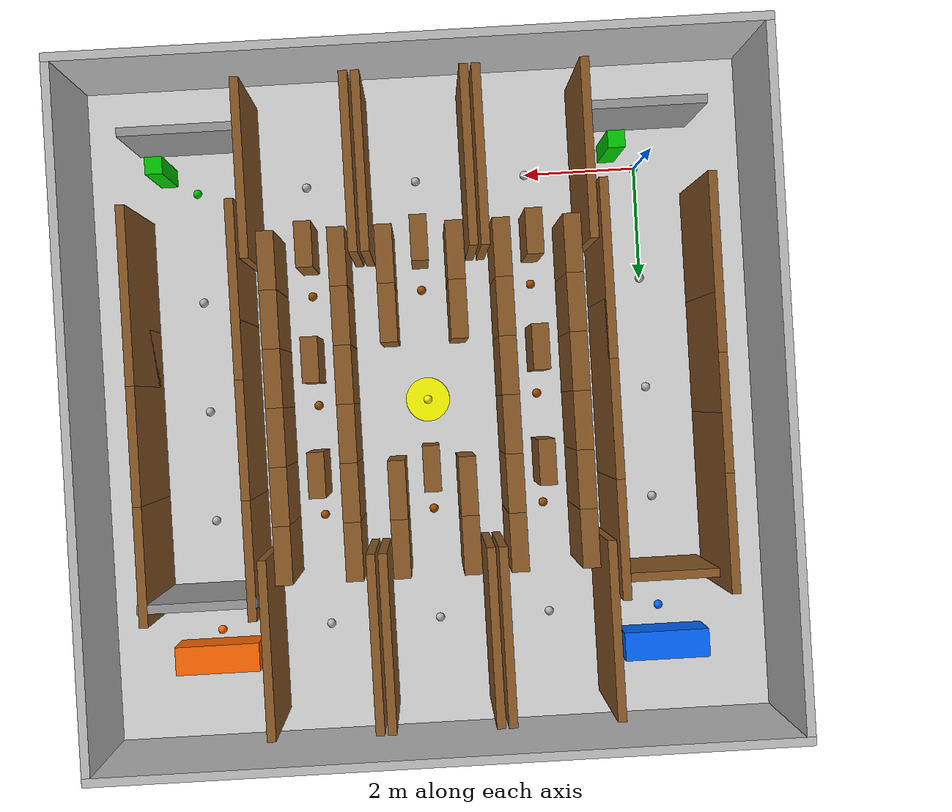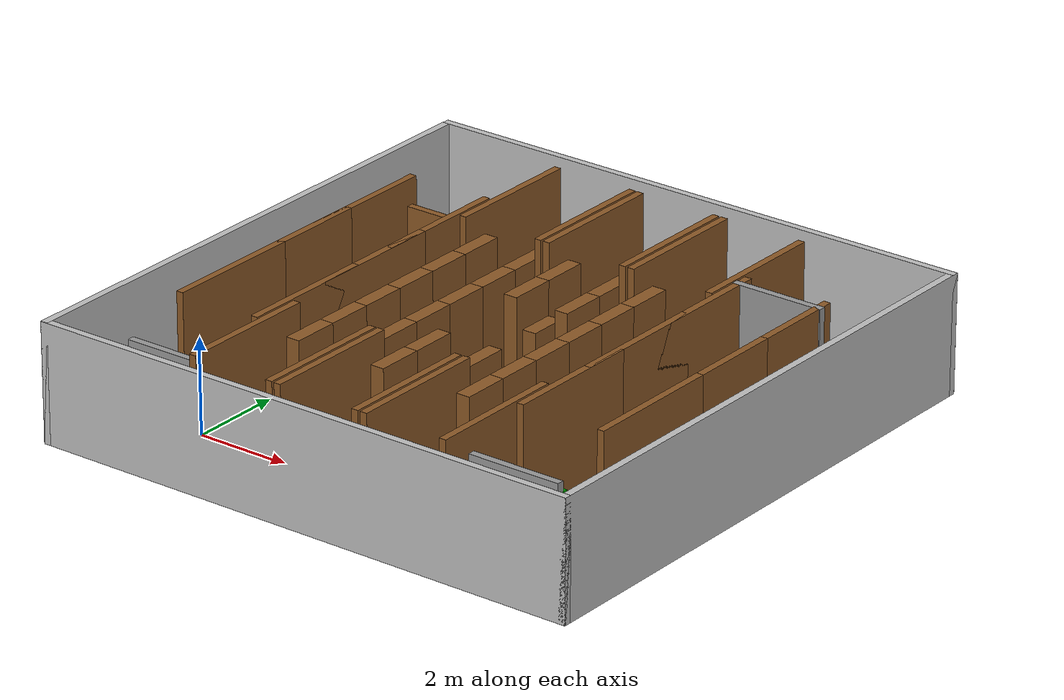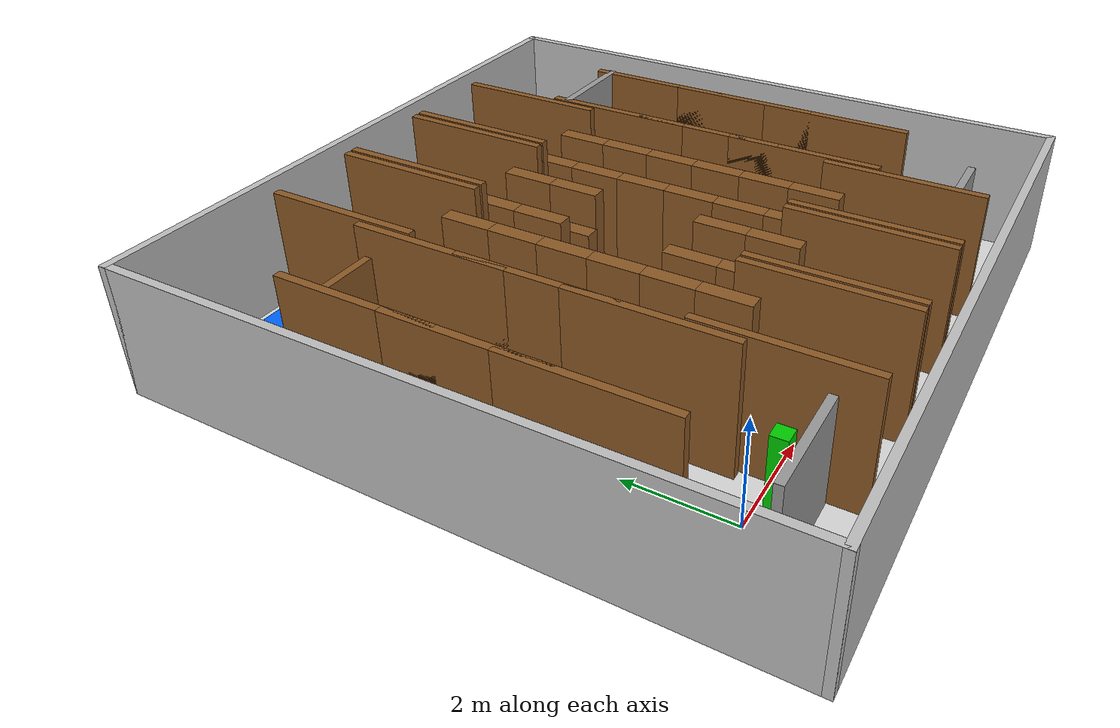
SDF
<?xml version="1.0" ?>
<sdf version="1.9">
  <world name="simple_5x5_grid">
    <plugin filename="gz-sim-physics-system" name="gz::sim::systems::Physics"/>
    <plugin filename="gz-sim-sensors-system" name="gz::sim::systems::Sensors">
      <render_engine>ogre2</render_engine>
    </plugin>
    <plugin filename="gz-sim-scene-broadcaster-system" name="gz::sim::systems::SceneBroadcaster"/>
    <light name="sun" type="directional">
      <cast_shadows>true</cast_shadows>
      <pose>0 0 10 0 0 0</pose>
      <diffuse>0.8 0.8 0.8 1</diffuse>
      <specular>0.2 0.2 0.2 1</specular>
      <direction>-0.5 0.1 -0.9</direction>
    </light>
    <physics name="default_physics" type="ode">
      <max_step_size>0.001</max_step_size>
      <real_time_factor>1.0</real_time_factor>
      <real_time_update_rate>1000</real_time_update_rate>
    </physics>
    <scene>
      <ambient>0.4 0.4 0.4 1.0</ambient>
      <background>0.7 0.7 0.9 1.0</background>
      <shadows>true</shadows>
    </scene>
    <gravity>0 0 -9.81</gravity>
    <model name="ground_plane">
      <static>true</static>
      <pose>4.0 4.0 0 0 0 0</pose>
      <link name="ground_link">
        <visual name="ground_visual">
          <geometry>
            <box>
              <size>12.0 12.0 0.01</size>
            </box>
          </geometry>
          <material>
            <ambient>0.85 0.85 0.85 1.0</ambient>
            <diffuse>0.85 0.85 0.85 1.0</diffuse>
          </material>
        </visual>
        <collision name="ground_visual_collision">
          <geometry>
            <box>
              <size>12.0 12.0 0.01</size>
            </box>
          </geometry>
        </collision>
        <collision name="ground_collision">
          <geometry>
            <plane>
              <normal>0 0 1</normal>
              <size>12.0 12.0</size>
            </plane>
          </geometry>
        </collision>
      </link>
    </model>
    <model name="wall_north">
      <static>true</static>
      <pose>4.0 10.0 1.25 0 0 0</pose>
      <link name="wall_north_link">
        <visual name="wall_north_visual">
          <geometry>
            <box>
              <size>12.15 0.15 2.5</size>
            </box>
          </geometry>
          <material>
            <ambient>0.75 0.75 0.75 1.0</ambient>
            <diffuse>0.75 0.75 0.75 1.0</diffuse>
          </material>
        </visual>
        <collision name="wall_north_visual_collision">
          <geometry>
            <box>
              <size>12.15 0.15 2.5</size>
            </box>
          </geometry>
        </collision>
      </link>
    </model>
    <model name="wall_south">
      <static>true</static>
      <pose>4.0 -2.0 1.25 0 0 0</pose>
      <link name="wall_south_link">
        <visual name="wall_south_visual">
          <geometry>
            <box>
              <size>12.15 0.15 2.5</size>
            </box>
          </geometry>
          <material>
            <ambient>0.75 0.75 0.75 1.0</ambient>
            <diffuse>0.75 0.75 0.75 1.0</diffuse>
          </material>
        </visual>
        <collision name="wall_south_visual_collision">
          <geometry>
            <box>
              <size>12.15 0.15 2.5</size>
            </box>
          </geometry>
        </collision>
      </link>
    </model>
    <model name="wall_east">
      <static>true</static>
      <pose>10.0 4.0 1.25 0 0 0</pose>
      <link name="wall_east_link">
        <visual name="wall_east_visual">
          <geometry>
            <box>
              <size>0.15 12.15 2.5</size>
            </box>
          </geometry>
          <material>
            <ambient>0.75 0.75 0.75 1.0</ambient>
            <diffuse>0.75 0.75 0.75 1.0</diffuse>
          </material>
        </visual>
        <collision name="wall_east_visual_collision">
          <geometry>
            <box>
              <size>0.15 12.15 2.5</size>
            </box>
          </geometry>
        </collision>
      </link>
    </model>
    <model name="wall_west">
      <static>true</static>
      <pose>-2.0 4.0 1.25 0 0 0</pose>
      <link name="wall_west_link">
        <visual name="wall_west_visual">
          <geometry>
            <box>
              <size>0.15 12.15 2.5</size>
            </box>
          </geometry>
          <material>
            <ambient>0.75 0.75 0.75 1.0</ambient>
            <diffuse>0.75 0.75 0.75 1.0</diffuse>
          </material>
        </visual>
        <collision name="wall_west_visual_collision">
          <geometry>
            <box>
              <size>0.15 12.15 2.5</size>
            </box>
          </geometry>
        </collision>
      </link>
    </model>
    <model name="dock_wall_DOCK_1_001">
      <static>true</static>
      <pose>0 -0.8 1.0 0 0 0</pose>
      <link name="dock_wall_DOCK_1_001_link">
        <visual name="dock_wall_DOCK_1_001_vis">
          <geometry>
            <box>
              <size>2.0 0.15 2.0</size>
            </box>
          </geometry>
          <material>
            <ambient>0.6 0.6 0.6 1.0</ambient>
            <diffuse>0.6 0.6 0.6 1.0</diffuse>
          </material>
        </visual>
        <collision name="dock_wall_DOCK_1_001_vis_collision">
          <geometry>
            <box>
              <size>2.0 0.15 2.0</size>
            </box>
          </geometry>
        </collision>
      </link>
    </model>
    <model name="charger_DOCK_1_002">
      <static>true</static>
      <pose>0.5 -0.3 0.75 0 0 0</pose>
      <link name="charger_DOCK_1_002_link">
        <visual name="charger_DOCK_1_002_vis">
          <geometry>
            <box>
              <size>0.3 0.3 1.5</size>
            </box>
          </geometry>
          <material>
            <ambient>0.0 0.8 0.0 1.0</ambient>
            <diffuse>0.0 0.8 0.0 1.0</diffuse>
          </material>
        </visual>
        <collision name="charger_DOCK_1_002_vis_collision">
          <geometry>
            <box>
              <size>0.3 0.3 1.5</size>
            </box>
          </geometry>
        </collision>
      </link>
    </model>
    <model name="aisle_L_N_01_003">
      <static>true</static>
      <pose>1.1 0 1.25 0 0 0</pose>
      <link name="aisle_L_N_01_003_link">
        <visual name="aisle_L_N_01_003_vis">
          <geometry>
            <box>
              <size>0.15 3.0 2.5</size>
            </box>
          </geometry>
          <material>
            <ambient>0.55 0.35 0.15 1.0</ambient>
            <diffuse>0.55 0.35 0.15 1.0</diffuse>
          </material>
        </visual>
        <collision name="aisle_L_N_01_003_vis_collision">
          <geometry>
            <box>
              <size>0.15 3.0 2.5</size>
            </box>
          </geometry>
        </collision>
      </link>
    </model>
    <model name="aisle_R_N_01_004">
      <static>true</static>
      <pose>2.9 0 1.25 0 0 0</pose>
      <link name="aisle_R_N_01_004_link">
        <visual name="aisle_R_N_01_004_vis">
          <geometry>
            <box>
              <size>0.15 3.0 2.5</size>
            </box>
          </geometry>
          <material>
            <ambient>0.55 0.35 0.15 1.0</ambient>
            <diffuse>0.55 0.35 0.15 1.0</diffuse>
          </material>
        </visual>
        <collision name="aisle_R_N_01_004_vis_collision">
          <geometry>
            <box>
              <size>0.15 3.0 2.5</size>
            </box>
          </geometry>
        </collision>
      </link>
    </model>
    <model name="aisle_L_N_02_005">
      <static>true</static>
      <pose>3.1 0 1.25 0 0 0</pose>
      <link name="aisle_L_N_02_005_link">
        <visual name="aisle_L_N_02_005_vis">
          <geometry>
            <box>
              <size>0.15 3.0 2.5</size>
            </box>
          </geometry>
          <material>
            <ambient>0.55 0.35 0.15 1.0</ambient>
            <diffuse>0.55 0.35 0.15 1.0</diffuse>
          </material>
        </visual>
        <collision name="aisle_L_N_02_005_vis_collision">
          <geometry>
            <box>
              <size>0.15 3.0 2.5</size>
            </box>
          </geometry>
        </collision>
      </link>
    </model>
    <model name="aisle_R_N_02_006">
      <static>true</static>
      <pose>4.9 0 1.25 0 0 0</pose>
      <link name="aisle_R_N_02_006_link">
        <visual name="aisle_R_N_02_006_vis">
          <geometry>
            <box>
              <size>0.15 3.0 2.5</size>
            </box>
          </geometry>
          <material>
            <ambient>0.55 0.35 0.15 1.0</ambient>
            <diffuse>0.55 0.35 0.15 1.0</diffuse>
          </material>
        </visual>
        <collision name="aisle_R_N_02_006_vis_collision">
          <geometry>
            <box>
              <size>0.15 3.0 2.5</size>
            </box>
          </geometry>
        </collision>
      </link>
    </model>
    <model name="aisle_L_N_03_007">
      <static>true</static>
      <pose>5.1 0 1.25 0 0 0</pose>
      <link name="aisle_L_N_03_007_link">
        <visual name="aisle_L_N_03_007_vis">
          <geometry>
            <box>
              <size>0.15 3.0 2.5</size>
            </box>
          </geometry>
          <material>
            <ambient>0.55 0.35 0.15 1.0</ambient>
            <diffuse>0.55 0.35 0.15 1.0</diffuse>
          </material>
        </visual>
        <collision name="aisle_L_N_03_007_vis_collision">
          <geometry>
            <box>
              <size>0.15 3.0 2.5</size>
            </box>
          </geometry>
        </collision>
      </link>
    </model>
    <model name="aisle_R_N_03_008">
      <static>true</static>
      <pose>6.9 0 1.25 0 0 0</pose>
      <link name="aisle_R_N_03_008_link">
        <visual name="aisle_R_N_03_008_vis">
          <geometry>
            <box>
              <size>0.15 3.0 2.5</size>
            </box>
          </geometry>
          <material>
            <ambient>0.55 0.35 0.15 1.0</ambient>
            <diffuse>0.55 0.35 0.15 1.0</diffuse>
          </material>
        </visual>
        <collision name="aisle_R_N_03_008_vis_collision">
          <geometry>
            <box>
              <size>0.15 3.0 2.5</size>
            </box>
          </geometry>
        </collision>
      </link>
    </model>
    <model name="dock_wall_DOCK_2_009">
      <static>true</static>
      <pose>8 -0.8 1.0 0 0 0</pose>
      <link name="dock_wall_DOCK_2_009_link">
        <visual name="dock_wall_DOCK_2_009_vis">
          <geometry>
            <box>
              <size>2.0 0.15 2.0</size>
            </box>
          </geometry>
          <material>
            <ambient>0.6 0.6 0.6 1.0</ambient>
            <diffuse>0.6 0.6 0.6 1.0</diffuse>
          </material>
        </visual>
        <collision name="dock_wall_DOCK_2_009_vis_collision">
          <geometry>
            <box>
              <size>2.0 0.15 2.0</size>
            </box>
          </geometry>
        </collision>
      </link>
    </model>
    <model name="charger_DOCK_2_010">
      <static>true</static>
      <pose>8.5 -0.3 0.75 0 0 0</pose>
      <link name="charger_DOCK_2_010_link">
        <visual name="charger_DOCK_2_010_vis">
          <geometry>
            <box>
              <size>0.3 0.3 1.5</size>
            </box>
          </geometry>
          <material>
            <ambient>0.0 0.8 0.0 1.0</ambient>
            <diffuse>0.0 0.8 0.0 1.0</diffuse>
          </material>
        </visual>
        <collision name="charger_DOCK_2_010_vis_collision">
          <geometry>
            <box>
              <size>0.3 0.3 1.5</size>
            </box>
          </geometry>
        </collision>
      </link>
    </model>
    <model name="aisle_L_N_10_011">
      <static>true</static>
      <pose>-0.9 2 1.25 0 0 0</pose>
      <link name="aisle_L_N_10_011_link">
        <visual name="aisle_L_N_10_011_vis">
          <geometry>
            <box>
              <size>0.15 3.0 2.5</size>
            </box>
          </geometry>
          <material>
            <ambient>0.55 0.35 0.15 1.0</ambient>
            <diffuse>0.55 0.35 0.15 1.0</diffuse>
          </material>
        </visual>
        <collision name="aisle_L_N_10_011_vis_collision">
          <geometry>
            <box>
              <size>0.15 3.0 2.5</size>
            </box>
          </geometry>
        </collision>
      </link>
    </model>
    <model name="aisle_R_N_10_012">
      <static>true</static>
      <pose>0.9 2 1.25 0 0 0</pose>
      <link name="aisle_R_N_10_012_link">
        <visual name="aisle_R_N_10_012_vis">
          <geometry>
            <box>
              <size>0.15 3.0 2.5</size>
            </box>
          </geometry>
          <material>
            <ambient>0.55 0.35 0.15 1.0</ambient>
            <diffuse>0.55 0.35 0.15 1.0</diffuse>
          </material>
        </visual>
        <collision name="aisle_R_N_10_012_vis_collision">
          <geometry>
            <box>
              <size>0.15 3.0 2.5</size>
            </box>
          </geometry>
        </collision>
      </link>
    </model>
    <model name="rack_S_11_013">
      <static>true</static>
      <pose>1.4 1.5 1.0 0 0 0</pose>
      <link name="rack_S_11_013_link">
        <visual name="rack_S_11_013_vis">
          <geometry>
            <box>
              <size>0.3 1.0 2.0</size>
            </box>
          </geometry>
          <material>
            <ambient>0.55 0.35 0.15 1.0</ambient>
            <diffuse>0.55 0.35 0.15 1.0</diffuse>
          </material>
        </visual>
        <collision name="rack_S_11_013_vis_collision">
          <geometry>
            <box>
              <size>0.3 1.0 2.0</size>
            </box>
          </geometry>
        </collision>
      </link>
    </model>
    <model name="rack_S_11_014">
      <static>true</static>
      <pose>1.4 2.5 1.0 0 0 0</pose>
      <link name="rack_S_11_014_link">
        <visual name="rack_S_11_014_vis">
          <geometry>
            <box>
              <size>0.3 1.0 2.0</size>
            </box>
          </geometry>
          <material>
            <ambient>0.55 0.35 0.15 1.0</ambient>
            <diffuse>0.55 0.35 0.15 1.0</diffuse>
          </material>
        </visual>
        <collision name="rack_S_11_014_vis_collision">
          <geometry>
            <box>
              <size>0.3 1.0 2.0</size>
            </box>
          </geometry>
        </collision>
      </link>
    </model>
    <model name="rack_S_11_015">
      <static>true</static>
      <pose>2.6 1.5 1.0 0 0 0</pose>
      <link name="rack_S_11_015_link">
        <visual name="rack_S_11_015_vis">
          <geometry>
            <box>
              <size>0.3 1.0 2.0</size>
            </box>
          </geometry>
          <material>
            <ambient>0.55 0.35 0.15 1.0</ambient>
            <diffuse>0.55 0.35 0.15 1.0</diffuse>
          </material>
        </visual>
        <collision name="rack_S_11_015_vis_collision">
          <geometry>
            <box>
              <size>0.3 1.0 2.0</size>
            </box>
          </geometry>
        </collision>
      </link>
    </model>
    <model name="rack_S_11_016">
      <static>true</static>
      <pose>2.6 2.5 1.0 0 0 0</pose>
      <link name="rack_S_11_016_link">
        <visual name="rack_S_11_016_vis">
          <geometry>
            <box>
              <size>0.3 1.0 2.0</size>
            </box>
          </geometry>
          <material>
            <ambient>0.55 0.35 0.15 1.0</ambient>
            <diffuse>0.55 0.35 0.15 1.0</diffuse>
          </material>
        </visual>
        <collision name="rack_S_11_016_vis_collision">
          <geometry>
            <box>
              <size>0.3 1.0 2.0</size>
            </box>
          </geometry>
        </collision>
      </link>
    </model>
    <model name="rack_S_11_017">
      <static>true</static>
      <pose>2.0 1.2 0.75 0 0 0</pose>
      <link name="rack_S_11_017_link">
        <visual name="rack_S_11_017_vis">
          <geometry>
            <box>
              <size>0.3 0.8 1.5</size>
            </box>
          </geometry>
          <material>
            <ambient>0.55 0.35 0.15 1.0</ambient>
            <diffuse>0.55 0.35 0.15 1.0</diffuse>
          </material>
        </visual>
        <collision name="rack_S_11_017_vis_collision">
          <geometry>
            <box>
              <size>0.3 0.8 1.5</size>
            </box>
          </geometry>
        </collision>
      </link>
    </model>
    <model name="rack_S_12_018">
      <static>true</static>
      <pose>3.4 1.5 1.0 0 0 0</pose>
      <link name="rack_S_12_018_link">
        <visual name="rack_S_12_018_vis">
          <geometry>
            <box>
              <size>0.3 1.0 2.0</size>
            </box>
          </geometry>
          <material>
            <ambient>0.55 0.35 0.15 1.0</ambient>
            <diffuse>0.55 0.35 0.15 1.0</diffuse>
          </material>
        </visual>
        <collision name="rack_S_12_018_vis_collision">
          <geometry>
            <box>
              <size>0.3 1.0 2.0</size>
            </box>
          </geometry>
        </collision>
      </link>
    </model>
    <model name="rack_S_12_019">
      <static>true</static>
      <pose>3.4 2.5 1.0 0 0 0</pose>
      <link name="rack_S_12_019_link">
        <visual name="rack_S_12_019_vis">
          <geometry>
            <box>
              <size>0.3 1.0 2.0</size>
            </box>
          </geometry>
          <material>
            <ambient>0.55 0.35 0.15 1.0</ambient>
            <diffuse>0.55 0.35 0.15 1.0</diffuse>
          </material>
        </visual>
        <collision name="rack_S_12_019_vis_collision">
          <geometry>
            <box>
              <size>0.3 1.0 2.0</size>
            </box>
          </geometry>
        </collision>
      </link>
    </model>
    <model name="rack_S_12_020">
      <static>true</static>
      <pose>4.6 1.5 1.0 0 0 0</pose>
      <link name="rack_S_12_020_link">
        <visual name="rack_S_12_020_vis">
          <geometry>
            <box>
              <size>0.3 1.0 2.0</size>
            </box>
          </geometry>
          <material>
            <ambient>0.55 0.35 0.15 1.0</ambient>
            <diffuse>0.55 0.35 0.15 1.0</diffuse>
          </material>
        </visual>
        <collision name="rack_S_12_020_vis_collision">
          <geometry>
            <box>
              <size>0.3 1.0 2.0</size>
            </box>
          </geometry>
        </collision>
      </link>
    </model>
    <model name="rack_S_12_021">
      <static>true</static>
      <pose>4.6 2.5 1.0 0 0 0</pose>
      <link name="rack_S_12_021_link">
        <visual name="rack_S_12_021_vis">
          <geometry>
            <box>
              <size>0.3 1.0 2.0</size>
            </box>
          </geometry>
          <material>
            <ambient>0.55 0.35 0.15 1.0</ambient>
            <diffuse>0.55 0.35 0.15 1.0</diffuse>
          </material>
        </visual>
        <collision name="rack_S_12_021_vis_collision">
          <geometry>
            <box>
              <size>0.3 1.0 2.0</size>
            </box>
          </geometry>
        </collision>
      </link>
    </model>
    <model name="rack_S_12_022">
      <static>true</static>
      <pose>4.0 1.2 0.75 0 0 0</pose>
      <link name="rack_S_12_022_link">
        <visual name="rack_S_12_022_vis">
          <geometry>
            <box>
              <size>0.3 0.8 1.5</size>
            </box>
          </geometry>
          <material>
            <ambient>0.55 0.35 0.15 1.0</ambient>
            <diffuse>0.55 0.35 0.15 1.0</diffuse>
          </material>
        </visual>
        <collision name="rack_S_12_022_vis_collision">
          <geometry>
            <box>
              <size>0.3 0.8 1.5</size>
            </box>
          </geometry>
        </collision>
      </link>
    </model>
    <model name="rack_S_13_023">
      <static>true</static>
      <pose>5.4 1.5 1.0 0 0 0</pose>
      <link name="rack_S_13_023_link">
        <visual name="rack_S_13_023_vis">
          <geometry>
            <box>
              <size>0.3 1.0 2.0</size>
            </box>
          </geometry>
          <material>
            <ambient>0.55 0.35 0.15 1.0</ambient>
            <diffuse>0.55 0.35 0.15 1.0</diffuse>
          </material>
        </visual>
        <collision name="rack_S_13_023_vis_collision">
          <geometry>
            <box>
              <size>0.3 1.0 2.0</size>
            </box>
          </geometry>
        </collision>
      </link>
    </model>
    <model name="rack_S_13_024">
      <static>true</static>
      <pose>5.4 2.5 1.0 0 0 0</pose>
      <link name="rack_S_13_024_link">
        <visual name="rack_S_13_024_vis">
          <geometry>
            <box>
              <size>0.3 1.0 2.0</size>
            </box>
          </geometry>
          <material>
            <ambient>0.55 0.35 0.15 1.0</ambient>
            <diffuse>0.55 0.35 0.15 1.0</diffuse>
          </material>
        </visual>
        <collision name="rack_S_13_024_vis_collision">
          <geometry>
            <box>
              <size>0.3 1.0 2.0</size>
            </box>
          </geometry>
        </collision>
      </link>
    </model>
    <model name="rack_S_13_025">
      <static>true</static>
      <pose>6.6 1.5 1.0 0 0 0</pose>
      <link name="rack_S_13_025_link">
        <visual name="rack_S_13_025_vis">
          <geometry>
            <box>
              <size>0.3 1.0 2.0</size>
            </box>
          </geometry>
          <material>
            <ambient>0.55 0.35 0.15 1.0</ambient>
            <diffuse>0.55 0.35 0.15 1.0</diffuse>
          </material>
        </visual>
        <collision name="rack_S_13_025_vis_collision">
          <geometry>
            <box>
              <size>0.3 1.0 2.0</size>
            </box>
          </geometry>
        </collision>
      </link>
    </model>
    <model name="rack_S_13_026">
      <static>true</static>
      <pose>6.6 2.5 1.0 0 0 0</pose>
      <link name="rack_S_13_026_link">
        <visual name="rack_S_13_026_vis">
          <geometry>
            <box>
              <size>0.3 1.0 2.0</size>
            </box>
          </geometry>
          <material>
            <ambient>0.55 0.35 0.15 1.0</ambient>
            <diffuse>0.55 0.35 0.15 1.0</diffuse>
          </material>
        </visual>
        <collision name="rack_S_13_026_vis_collision">
          <geometry>
            <box>
              <size>0.3 1.0 2.0</size>
            </box>
          </geometry>
        </collision>
      </link>
    </model>
    <model name="rack_S_13_027">
      <static>true</static>
      <pose>6.0 1.2 0.75 0 0 0</pose>
      <link name="rack_S_13_027_link">
        <visual name="rack_S_13_027_vis">
          <geometry>
            <box>
              <size>0.3 0.8 1.5</size>
            </box>
          </geometry>
          <material>
            <ambient>0.55 0.35 0.15 1.0</ambient>
            <diffuse>0.55 0.35 0.15 1.0</diffuse>
          </material>
        </visual>
        <collision name="rack_S_13_027_vis_collision">
          <geometry>
            <box>
              <size>0.3 0.8 1.5</size>
            </box>
          </geometry>
        </collision>
      </link>
    </model>
    <model name="aisle_L_N_14_028">
      <static>true</static>
      <pose>7.1 2 1.25 0 0 0</pose>
      <link name="aisle_L_N_14_028_link">
        <visual name="aisle_L_N_14_028_vis">
          <geometry>
            <box>
              <size>0.15 3.0 2.5</size>
            </box>
          </geometry>
          <material>
            <ambient>0.55 0.35 0.15 1.0</ambient>
            <diffuse>0.55 0.35 0.15 1.0</diffuse>
          </material>
        </visual>
        <collision name="aisle_L_N_14_028_vis_collision">
          <geometry>
            <box>
              <size>0.15 3.0 2.5</size>
            </box>
          </geometry>
        </collision>
      </link>
    </model>
    <model name="aisle_R_N_14_029">
      <static>true</static>
      <pose>8.9 2 1.25 0 0 0</pose>
      <link name="aisle_R_N_14_029_link">
        <visual name="aisle_R_N_14_029_vis">
          <geometry>
            <box>
              <size>0.15 3.0 2.5</size>
            </box>
          </geometry>
          <material>
            <ambient>0.55 0.35 0.15 1.0</ambient>
            <diffuse>0.55 0.35 0.15 1.0</diffuse>
          </material>
        </visual>
        <collision name="aisle_R_N_14_029_vis_collision">
          <geometry>
            <box>
              <size>0.15 3.0 2.5</size>
            </box>
          </geometry>
        </collision>
      </link>
    </model>
    <model name="aisle_L_N_20_030">
      <static>true</static>
      <pose>-0.9 4 1.25 0 0 0</pose>
      <link name="aisle_L_N_20_030_link">
        <visual name="aisle_L_N_20_030_vis">
          <geometry>
            <box>
              <size>0.15 3.0 2.5</size>
            </box>
          </geometry>
          <material>
            <ambient>0.55 0.35 0.15 1.0</ambient>
            <diffuse>0.55 0.35 0.15 1.0</diffuse>
          </material>
        </visual>
        <collision name="aisle_L_N_20_030_vis_collision">
          <geometry>
            <box>
              <size>0.15 3.0 2.5</size>
            </box>
          </geometry>
        </collision>
      </link>
    </model>
    <model name="aisle_R_N_20_031">
      <static>true</static>
      <pose>0.9 4 1.25 0 0 0</pose>
      <link name="aisle_R_N_20_031_link">
        <visual name="aisle_R_N_20_031_vis">
          <geometry>
            <box>
              <size>0.15 3.0 2.5</size>
            </box>
          </geometry>
          <material>
            <ambient>0.55 0.35 0.15 1.0</ambient>
            <diffuse>0.55 0.35 0.15 1.0</diffuse>
          </material>
        </visual>
        <collision name="aisle_R_N_20_031_vis_collision">
          <geometry>
            <box>
              <size>0.15 3.0 2.5</size>
            </box>
          </geometry>
        </collision>
      </link>
    </model>
    <model name="rack_S_21_032">
      <static>true</static>
      <pose>1.4 3.5 1.0 0 0 0</pose>
      <link name="rack_S_21_032_link">
        <visual name="rack_S_21_032_vis">
          <geometry>
            <box>
              <size>0.3 1.0 2.0</size>
            </box>
          </geometry>
          <material>
            <ambient>0.55 0.35 0.15 1.0</ambient>
            <diffuse>0.55 0.35 0.15 1.0</diffuse>
          </material>
        </visual>
        <collision name="rack_S_21_032_vis_collision">
          <geometry>
            <box>
              <size>0.3 1.0 2.0</size>
            </box>
          </geometry>
        </collision>
      </link>
    </model>
    <model name="rack_S_21_033">
      <static>true</static>
      <pose>1.4 4.5 1.0 0 0 0</pose>
      <link name="rack_S_21_033_link">
        <visual name="rack_S_21_033_vis">
          <geometry>
            <box>
              <size>0.3 1.0 2.0</size>
            </box>
          </geometry>
          <material>
            <ambient>0.55 0.35 0.15 1.0</ambient>
            <diffuse>0.55 0.35 0.15 1.0</diffuse>
          </material>
        </visual>
        <collision name="rack_S_21_033_vis_collision">
          <geometry>
            <box>
              <size>0.3 1.0 2.0</size>
            </box>
          </geometry>
        </collision>
      </link>
    </model>
    <model name="rack_S_21_034">
      <static>true</static>
      <pose>2.6 3.5 1.0 0 0 0</pose>
      <link name="rack_S_21_034_link">
        <visual name="rack_S_21_034_vis">
          <geometry>
            <box>
              <size>0.3 1.0 2.0</size>
            </box>
          </geometry>
          <material>
            <ambient>0.55 0.35 0.15 1.0</ambient>
            <diffuse>0.55 0.35 0.15 1.0</diffuse>
          </material>
        </visual>
        <collision name="rack_S_21_034_vis_collision">
          <geometry>
            <box>
              <size>0.3 1.0 2.0</size>
            </box>
          </geometry>
        </collision>
      </link>
    </model>
    <model name="rack_S_21_035">
      <static>true</static>
      <pose>2.6 4.5 1.0 0 0 0</pose>
      <link name="rack_S_21_035_link">
        <visual name="rack_S_21_035_vis">
          <geometry>
            <box>
              <size>0.3 1.0 2.0</size>
            </box>
          </geometry>
          <material>
            <ambient>0.55 0.35 0.15 1.0</ambient>
            <diffuse>0.55 0.35 0.15 1.0</diffuse>
          </material>
        </visual>
        <collision name="rack_S_21_035_vis_collision">
          <geometry>
            <box>
              <size>0.3 1.0 2.0</size>
            </box>
          </geometry>
        </collision>
      </link>
    </model>
    <model name="rack_S_21_036">
      <static>true</static>
      <pose>2.0 3.2 0.75 0 0 0</pose>
      <link name="rack_S_21_036_link">
        <visual name="rack_S_21_036_vis">
          <geometry>
            <box>
              <size>0.3 0.8 1.5</size>
            </box>
          </geometry>
          <material>
            <ambient>0.55 0.35 0.15 1.0</ambient>
            <diffuse>0.55 0.35 0.15 1.0</diffuse>
          </material>
        </visual>
        <collision name="rack_S_21_036_vis_collision">
          <geometry>
            <box>
              <size>0.3 0.8 1.5</size>
            </box>
          </geometry>
        </collision>
      </link>
    </model>
    <model name="hub_HUB_037">
      <static>true</static>
      <pose>4 4 0.01 0 0 0</pose>
      <link name="hub_HUB_037_link">
        <visual name="hub_HUB_037_vis">
          <geometry>
            <cylinder>
              <radius>0.4</radius>
              <length>0.02</length>
            </cylinder>
          </geometry>
          <material>
            <ambient>1.0 1.0 0.0 1.0</ambient>
            <diffuse>1.0 1.0 0.0 1.0</diffuse>
          </material>
        </visual>
        <collision name="hub_HUB_037_vis_collision">
          <geometry>
            <cylinder>
              <radius>0.4</radius>
              <length>0.02</length>
            </cylinder>
          </geometry>
        </collision>
      </link>
    </model>
    <model name="rack_S_23_038">
      <static>true</static>
      <pose>5.4 3.5 1.0 0 0 0</pose>
      <link name="rack_S_23_038_link">
        <visual name="rack_S_23_038_vis">
          <geometry>
            <box>
              <size>0.3 1.0 2.0</size>
            </box>
          </geometry>
          <material>
            <ambient>0.55 0.35 0.15 1.0</ambient>
            <diffuse>0.55 0.35 0.15 1.0</diffuse>
          </material>
        </visual>
        <collision name="rack_S_23_038_vis_collision">
          <geometry>
            <box>
              <size>0.3 1.0 2.0</size>
            </box>
          </geometry>
        </collision>
      </link>
    </model>
    <model name="rack_S_23_039">
      <static>true</static>
      <pose>5.4 4.5 1.0 0 0 0</pose>
      <link name="rack_S_23_039_link">
        <visual name="rack_S_23_039_vis">
          <geometry>
            <box>
              <size>0.3 1.0 2.0</size>
            </box>
          </geometry>
          <material>
            <ambient>0.55 0.35 0.15 1.0</ambient>
            <diffuse>0.55 0.35 0.15 1.0</diffuse>
          </material>
        </visual>
        <collision name="rack_S_23_039_vis_collision">
          <geometry>
            <box>
              <size>0.3 1.0 2.0</size>
            </box>
          </geometry>
        </collision>
      </link>
    </model>
    <model name="rack_S_23_040">
      <static>true</static>
      <pose>6.6 3.5 1.0 0 0 0</pose>
      <link name="rack_S_23_040_link">
        <visual name="rack_S_23_040_vis">
          <geometry>
            <box>
              <size>0.3 1.0 2.0</size>
            </box>
          </geometry>
          <material>
            <ambient>0.55 0.35 0.15 1.0</ambient>
            <diffuse>0.55 0.35 0.15 1.0</diffuse>
          </material>
        </visual>
        <collision name="rack_S_23_040_vis_collision">
          <geometry>
            <box>
              <size>0.3 1.0 2.0</size>
            </box>
          </geometry>
        </collision>
      </link>
    </model>
    <model name="rack_S_23_041">
      <static>true</static>
      <pose>6.6 4.5 1.0 0 0 0</pose>
      <link name="rack_S_23_041_link">
        <visual name="rack_S_23_041_vis">
          <geometry>
            <box>
              <size>0.3 1.0 2.0</size>
            </box>
          </geometry>
          <material>
            <ambient>0.55 0.35 0.15 1.0</ambient>
            <diffuse>0.55 0.35 0.15 1.0</diffuse>
          </material>
        </visual>
        <collision name="rack_S_23_041_vis_collision">
          <geometry>
            <box>
              <size>0.3 1.0 2.0</size>
            </box>
          </geometry>
        </collision>
      </link>
    </model>
    <model name="rack_S_23_042">
      <static>true</static>
      <pose>6.0 3.2 0.75 0 0 0</pose>
      <link name="rack_S_23_042_link">
        <visual name="rack_S_23_042_vis">
          <geometry>
            <box>
              <size>0.3 0.8 1.5</size>
            </box>
          </geometry>
          <material>
            <ambient>0.55 0.35 0.15 1.0</ambient>
            <diffuse>0.55 0.35 0.15 1.0</diffuse>
          </material>
        </visual>
        <collision name="rack_S_23_042_vis_collision">
          <geometry>
            <box>
              <size>0.3 0.8 1.5</size>
            </box>
          </geometry>
        </collision>
      </link>
    </model>
    <model name="aisle_L_N_24_043">
      <static>true</static>
      <pose>7.1 4 1.25 0 0 0</pose>
      <link name="aisle_L_N_24_043_link">
        <visual name="aisle_L_N_24_043_vis">
          <geometry>
            <box>
              <size>0.15 3.0 2.5</size>
            </box>
          </geometry>
          <material>
            <ambient>0.55 0.35 0.15 1.0</ambient>
            <diffuse>0.55 0.35 0.15 1.0</diffuse>
          </material>
        </visual>
        <collision name="aisle_L_N_24_043_vis_collision">
          <geometry>
            <box>
              <size>0.15 3.0 2.5</size>
            </box>
          </geometry>
        </collision>
      </link>
    </model>
    <model name="aisle_R_N_24_044">
      <static>true</static>
      <pose>8.9 4 1.25 0 0 0</pose>
      <link name="aisle_R_N_24_044_link">
        <visual name="aisle_R_N_24_044_vis">
          <geometry>
            <box>
              <size>0.15 3.0 2.5</size>
            </box>
          </geometry>
          <material>
            <ambient>0.55 0.35 0.15 1.0</ambient>
            <diffuse>0.55 0.35 0.15 1.0</diffuse>
          </material>
        </visual>
        <collision name="aisle_R_N_24_044_vis_collision">
          <geometry>
            <box>
              <size>0.15 3.0 2.5</size>
            </box>
          </geometry>
        </collision>
      </link>
    </model>
    <model name="aisle_L_N_30_045">
      <static>true</static>
      <pose>-0.9 6 1.25 0 0 0</pose>
      <link name="aisle_L_N_30_045_link">
        <visual name="aisle_L_N_30_045_vis">
          <geometry>
            <box>
              <size>0.15 3.0 2.5</size>
            </box>
          </geometry>
          <material>
            <ambient>0.55 0.35 0.15 1.0</ambient>
            <diffuse>0.55 0.35 0.15 1.0</diffuse>
          </material>
        </visual>
        <collision name="aisle_L_N_30_045_vis_collision">
          <geometry>
            <box>
              <size>0.15 3.0 2.5</size>
            </box>
          </geometry>
        </collision>
      </link>
    </model>
    <model name="aisle_R_N_30_046">
      <static>true</static>
      <pose>0.9 6 1.25 0 0 0</pose>
      <link name="aisle_R_N_30_046_link">
        <visual name="aisle_R_N_30_046_vis">
          <geometry>
            <box>
              <size>0.15 3.0 2.5</size>
            </box>
          </geometry>
          <material>
            <ambient>0.55 0.35 0.15 1.0</ambient>
            <diffuse>0.55 0.35 0.15 1.0</diffuse>
          </material>
        </visual>
        <collision name="aisle_R_N_30_046_vis_collision">
          <geometry>
            <box>
              <size>0.15 3.0 2.5</size>
            </box>
          </geometry>
        </collision>
      </link>
    </model>
    <model name="rack_S_31_047">
      <static>true</static>
      <pose>1.4 5.5 1.0 0 0 0</pose>
      <link name="rack_S_31_047_link">
        <visual name="rack_S_31_047_vis">
          <geometry>
            <box>
              <size>0.3 1.0 2.0</size>
            </box>
          </geometry>
          <material>
            <ambient>0.55 0.35 0.15 1.0</ambient>
            <diffuse>0.55 0.35 0.15 1.0</diffuse>
          </material>
        </visual>
        <collision name="rack_S_31_047_vis_collision">
          <geometry>
            <box>
              <size>0.3 1.0 2.0</size>
            </box>
          </geometry>
        </collision>
      </link>
    </model>
    <model name="rack_S_31_048">
      <static>true</static>
      <pose>1.4 6.5 1.0 0 0 0</pose>
      <link name="rack_S_31_048_link">
        <visual name="rack_S_31_048_vis">
          <geometry>
            <box>
              <size>0.3 1.0 2.0</size>
            </box>
          </geometry>
          <material>
            <ambient>0.55 0.35 0.15 1.0</ambient>
            <diffuse>0.55 0.35 0.15 1.0</diffuse>
          </material>
        </visual>
        <collision name="rack_S_31_048_vis_collision">
          <geometry>
            <box>
              <size>0.3 1.0 2.0</size>
            </box>
          </geometry>
        </collision>
      </link>
    </model>
    <model name="rack_S_31_049">
      <static>true</static>
      <pose>2.6 5.5 1.0 0 0 0</pose>
      <link name="rack_S_31_049_link">
        <visual name="rack_S_31_049_vis">
          <geometry>
            <box>
              <size>0.3 1.0 2.0</size>
            </box>
          </geometry>
          <material>
            <ambient>0.55 0.35 0.15 1.0</ambient>
            <diffuse>0.55 0.35 0.15 1.0</diffuse>
          </material>
        </visual>
        <collision name="rack_S_31_049_vis_collision">
          <geometry>
            <box>
              <size>0.3 1.0 2.0</size>
            </box>
          </geometry>
        </collision>
      </link>
    </model>
    <model name="rack_S_31_050">
      <static>true</static>
      <pose>2.6 6.5 1.0 0 0 0</pose>
      <link name="rack_S_31_050_link">
        <visual name="rack_S_31_050_vis">
          <geometry>
            <box>
              <size>0.3 1.0 2.0</size>
            </box>
          </geometry>
          <material>
            <ambient>0.55 0.35 0.15 1.0</ambient>
            <diffuse>0.55 0.35 0.15 1.0</diffuse>
          </material>
        </visual>
        <collision name="rack_S_31_050_vis_collision">
          <geometry>
            <box>
              <size>0.3 1.0 2.0</size>
            </box>
          </geometry>
        </collision>
      </link>
    </model>
    <model name="rack_S_31_051">
      <static>true</static>
      <pose>2.0 5.2 0.75 0 0 0</pose>
      <link name="rack_S_31_051_link">
        <visual name="rack_S_31_051_vis">
          <geometry>
            <box>
              <size>0.3 0.8 1.5</size>
            </box>
          </geometry>
          <material>
            <ambient>0.55 0.35 0.15 1.0</ambient>
            <diffuse>0.55 0.35 0.15 1.0</diffuse>
          </material>
        </visual>
        <collision name="rack_S_31_051_vis_collision">
          <geometry>
            <box>
              <size>0.3 0.8 1.5</size>
            </box>
          </geometry>
        </collision>
      </link>
    </model>
    <model name="rack_S_32_052">
      <static>true</static>
      <pose>3.4 5.5 1.0 0 0 0</pose>
      <link name="rack_S_32_052_link">
        <visual name="rack_S_32_052_vis">
          <geometry>
            <box>
              <size>0.3 1.0 2.0</size>
            </box>
          </geometry>
          <material>
            <ambient>0.55 0.35 0.15 1.0</ambient>
            <diffuse>0.55 0.35 0.15 1.0</diffuse>
          </material>
        </visual>
        <collision name="rack_S_32_052_vis_collision">
          <geometry>
            <box>
              <size>0.3 1.0 2.0</size>
            </box>
          </geometry>
        </collision>
      </link>
    </model>
    <model name="rack_S_32_053">
      <static>true</static>
      <pose>3.4 6.5 1.0 0 0 0</pose>
      <link name="rack_S_32_053_link">
        <visual name="rack_S_32_053_vis">
          <geometry>
            <box>
              <size>0.3 1.0 2.0</size>
            </box>
          </geometry>
          <material>
            <ambient>0.55 0.35 0.15 1.0</ambient>
            <diffuse>0.55 0.35 0.15 1.0</diffuse>
          </material>
        </visual>
        <collision name="rack_S_32_053_vis_collision">
          <geometry>
            <box>
              <size>0.3 1.0 2.0</size>
            </box>
          </geometry>
        </collision>
      </link>
    </model>
    <model name="rack_S_32_054">
      <static>true</static>
      <pose>4.6 5.5 1.0 0 0 0</pose>
      <link name="rack_S_32_054_link">
        <visual name="rack_S_32_054_vis">
          <geometry>
            <box>
              <size>0.3 1.0 2.0</size>
            </box>
          </geometry>
          <material>
            <ambient>0.55 0.35 0.15 1.0</ambient>
            <diffuse>0.55 0.35 0.15 1.0</diffuse>
          </material>
        </visual>
        <collision name="rack_S_32_054_vis_collision">
          <geometry>
            <box>
              <size>0.3 1.0 2.0</size>
            </box>
          </geometry>
        </collision>
      </link>
    </model>
    <model name="rack_S_32_055">
      <static>true</static>
      <pose>4.6 6.5 1.0 0 0 0</pose>
      <link name="rack_S_32_055_link">
        <visual name="rack_S_32_055_vis">
          <geometry>
            <box>
              <size>0.3 1.0 2.0</size>
            </box>
          </geometry>
          <material>
            <ambient>0.55 0.35 0.15 1.0</ambient>
            <diffuse>0.55 0.35 0.15 1.0</diffuse>
          </material>
        </visual>
        <collision name="rack_S_32_055_vis_collision">
          <geometry>
            <box>
              <size>0.3 1.0 2.0</size>
            </box>
          </geometry>
        </collision>
      </link>
    </model>
    <model name="rack_S_32_056">
      <static>true</static>
      <pose>4.0 5.2 0.75 0 0 0</pose>
      <link name="rack_S_32_056_link">
        <visual name="rack_S_32_056_vis">
          <geometry>
            <box>
              <size>0.3 0.8 1.5</size>
            </box>
          </geometry>
          <material>
            <ambient>0.55 0.35 0.15 1.0</ambient>
            <diffuse>0.55 0.35 0.15 1.0</diffuse>
          </material>
        </visual>
        <collision name="rack_S_32_056_vis_collision">
          <geometry>
            <box>
              <size>0.3 0.8 1.5</size>
            </box>
          </geometry>
        </collision>
      </link>
    </model>
    <model name="rack_S_33_057">
      <static>true</static>
      <pose>5.4 5.5 1.0 0 0 0</pose>
      <link name="rack_S_33_057_link">
        <visual name="rack_S_33_057_vis">
          <geometry>
            <box>
              <size>0.3 1.0 2.0</size>
            </box>
          </geometry>
          <material>
            <ambient>0.55 0.35 0.15 1.0</ambient>
            <diffuse>0.55 0.35 0.15 1.0</diffuse>
          </material>
        </visual>
        <collision name="rack_S_33_057_vis_collision">
          <geometry>
            <box>
              <size>0.3 1.0 2.0</size>
            </box>
          </geometry>
        </collision>
      </link>
    </model>
    <model name="rack_S_33_058">
      <static>true</static>
      <pose>5.4 6.5 1.0 0 0 0</pose>
      <link name="rack_S_33_058_link">
        <visual name="rack_S_33_058_vis">
          <geometry>
            <box>
              <size>0.3 1.0 2.0</size>
            </box>
          </geometry>
          <material>
            <ambient>0.55 0.35 0.15 1.0</ambient>
            <diffuse>0.55 0.35 0.15 1.0</diffuse>
          </material>
        </visual>
        <collision name="rack_S_33_058_vis_collision">
          <geometry>
            <box>
              <size>0.3 1.0 2.0</size>
            </box>
          </geometry>
        </collision>
      </link>
    </model>
    <model name="rack_S_33_059">
      <static>true</static>
      <pose>6.6 5.5 1.0 0 0 0</pose>
      <link name="rack_S_33_059_link">
        <visual name="rack_S_33_059_vis">
          <geometry>
            <box>
              <size>0.3 1.0 2.0</size>
            </box>
          </geometry>
          <material>
            <ambient>0.55 0.35 0.15 1.0</ambient>
            <diffuse>0.55 0.35 0.15 1.0</diffuse>
          </material>
        </visual>
        <collision name="rack_S_33_059_vis_collision">
          <geometry>
            <box>
              <size>0.3 1.0 2.0</size>
            </box>
          </geometry>
        </collision>
      </link>
    </model>
    <model name="rack_S_33_060">
      <static>true</static>
      <pose>6.6 6.5 1.0 0 0 0</pose>
      <link name="rack_S_33_060_link">
        <visual name="rack_S_33_060_vis">
          <geometry>
            <box>
              <size>0.3 1.0 2.0</size>
            </box>
          </geometry>
          <material>
            <ambient>0.55 0.35 0.15 1.0</ambient>
            <diffuse>0.55 0.35 0.15 1.0</diffuse>
          </material>
        </visual>
        <collision name="rack_S_33_060_vis_collision">
          <geometry>
            <box>
              <size>0.3 1.0 2.0</size>
            </box>
          </geometry>
        </collision>
      </link>
    </model>
    <model name="rack_S_33_061">
      <static>true</static>
      <pose>6.0 5.2 0.75 0 0 0</pose>
      <link name="rack_S_33_061_link">
        <visual name="rack_S_33_061_vis">
          <geometry>
            <box>
              <size>0.3 0.8 1.5</size>
            </box>
          </geometry>
          <material>
            <ambient>0.55 0.35 0.15 1.0</ambient>
            <diffuse>0.55 0.35 0.15 1.0</diffuse>
          </material>
        </visual>
        <collision name="rack_S_33_061_vis_collision">
          <geometry>
            <box>
              <size>0.3 0.8 1.5</size>
            </box>
          </geometry>
        </collision>
      </link>
    </model>
    <model name="aisle_L_N_34_062">
      <static>true</static>
      <pose>7.1 6 1.25 0 0 0</pose>
      <link name="aisle_L_N_34_062_link">
        <visual name="aisle_L_N_34_062_vis">
          <geometry>
            <box>
              <size>0.15 3.0 2.5</size>
            </box>
          </geometry>
          <material>
            <ambient>0.55 0.35 0.15 1.0</ambient>
            <diffuse>0.55 0.35 0.15 1.0</diffuse>
          </material>
        </visual>
        <collision name="aisle_L_N_34_062_vis_collision">
          <geometry>
            <box>
              <size>0.15 3.0 2.5</size>
            </box>
          </geometry>
        </collision>
      </link>
    </model>
    <model name="aisle_R_N_34_063">
      <static>true</static>
      <pose>8.9 6 1.25 0 0 0</pose>
      <link name="aisle_R_N_34_063_link">
        <visual name="aisle_R_N_34_063_vis">
          <geometry>
            <box>
              <size>0.15 3.0 2.5</size>
            </box>
          </geometry>
          <material>
            <ambient>0.55 0.35 0.15 1.0</ambient>
            <diffuse>0.55 0.35 0.15 1.0</diffuse>
          </material>
        </visual>
        <collision name="aisle_R_N_34_063_vis_collision">
          <geometry>
            <box>
              <size>0.15 3.0 2.5</size>
            </box>
          </geometry>
        </collision>
      </link>
    </model>
    <model name="pick_table_PICK_1_064">
      <static>true</static>
      <pose>0 8.6 0.4 0 0 0</pose>
      <link name="pick_table_PICK_1_064_link">
        <visual name="pick_table_PICK_1_064_vis">
          <geometry>
            <box>
              <size>1.5 0.5 0.8</size>
            </box>
          </geometry>
          <material>
            <ambient>0.0 0.4 1.0 1.0</ambient>
            <diffuse>0.0 0.4 1.0 1.0</diffuse>
          </material>
        </visual>
        <collision name="pick_table_PICK_1_064_vis_collision">
          <geometry>
            <box>
              <size>1.5 0.5 0.8</size>
            </box>
          </geometry>
        </collision>
      </link>
    </model>
    <model name="pick_shelf_PICK_1_065">
      <static>true</static>
      <pose>0 7.2 1.0 0 0 0</pose>
      <link name="pick_shelf_PICK_1_065_link">
        <visual name="pick_shelf_PICK_1_065_vis">
          <geometry>
            <box>
              <size>1.5 0.15 2.0</size>
            </box>
          </geometry>
          <material>
            <ambient>0.55 0.35 0.15 1.0</ambient>
            <diffuse>0.55 0.35 0.15 1.0</diffuse>
          </material>
        </visual>
        <collision name="pick_shelf_PICK_1_065_vis_collision">
          <geometry>
            <box>
              <size>1.5 0.15 2.0</size>
            </box>
          </geometry>
        </collision>
      </link>
    </model>
    <model name="aisle_L_N_41_066">
      <static>true</static>
      <pose>1.1 8 1.25 0 0 0</pose>
      <link name="aisle_L_N_41_066_link">
        <visual name="aisle_L_N_41_066_vis">
          <geometry>
            <box>
              <size>0.15 3.0 2.5</size>
            </box>
          </geometry>
          <material>
            <ambient>0.55 0.35 0.15 1.0</ambient>
            <diffuse>0.55 0.35 0.15 1.0</diffuse>
          </material>
        </visual>
        <collision name="aisle_L_N_41_066_vis_collision">
          <geometry>
            <box>
              <size>0.15 3.0 2.5</size>
            </box>
          </geometry>
        </collision>
      </link>
    </model>
    <model name="aisle_R_N_41_067">
      <static>true</static>
      <pose>2.9 8 1.25 0 0 0</pose>
      <link name="aisle_R_N_41_067_link">
        <visual name="aisle_R_N_41_067_vis">
          <geometry>
            <box>
              <size>0.15 3.0 2.5</size>
            </box>
          </geometry>
          <material>
            <ambient>0.55 0.35 0.15 1.0</ambient>
            <diffuse>0.55 0.35 0.15 1.0</diffuse>
          </material>
        </visual>
        <collision name="aisle_R_N_41_067_vis_collision">
          <geometry>
            <box>
              <size>0.15 3.0 2.5</size>
            </box>
          </geometry>
        </collision>
      </link>
    </model>
    <model name="aisle_L_N_42_068">
      <static>true</static>
      <pose>3.1 8 1.25 0 0 0</pose>
      <link name="aisle_L_N_42_068_link">
        <visual name="aisle_L_N_42_068_vis">
          <geometry>
            <box>
              <size>0.15 3.0 2.5</size>
            </box>
          </geometry>
          <material>
            <ambient>0.55 0.35 0.15 1.0</ambient>
            <diffuse>0.55 0.35 0.15 1.0</diffuse>
          </material>
        </visual>
        <collision name="aisle_L_N_42_068_vis_collision">
          <geometry>
            <box>
              <size>0.15 3.0 2.5</size>
            </box>
          </geometry>
        </collision>
      </link>
    </model>
    <model name="aisle_R_N_42_069">
      <static>true</static>
      <pose>4.9 8 1.25 0 0 0</pose>
      <link name="aisle_R_N_42_069_link">
        <visual name="aisle_R_N_42_069_vis">
          <geometry>
            <box>
              <size>0.15 3.0 2.5</size>
            </box>
          </geometry>
          <material>
            <ambient>0.55 0.35 0.15 1.0</ambient>
            <diffuse>0.55 0.35 0.15 1.0</diffuse>
          </material>
        </visual>
        <collision name="aisle_R_N_42_069_vis_collision">
          <geometry>
            <box>
              <size>0.15 3.0 2.5</size>
            </box>
          </geometry>
        </collision>
      </link>
    </model>
    <model name="aisle_L_N_43_070">
      <static>true</static>
      <pose>5.1 8 1.25 0 0 0</pose>
      <link name="aisle_L_N_43_070_link">
        <visual name="aisle_L_N_43_070_vis">
          <geometry>
            <box>
              <size>0.15 3.0 2.5</size>
            </box>
          </geometry>
          <material>
            <ambient>0.55 0.35 0.15 1.0</ambient>
            <diffuse>0.55 0.35 0.15 1.0</diffuse>
          </material>
        </visual>
        <collision name="aisle_L_N_43_070_vis_collision">
          <geometry>
            <box>
              <size>0.15 3.0 2.5</size>
            </box>
          </geometry>
        </collision>
      </link>
    </model>
    <model name="aisle_R_N_43_071">
      <static>true</static>
      <pose>6.9 8 1.25 0 0 0</pose>
      <link name="aisle_R_N_43_071_link">
        <visual name="aisle_R_N_43_071_vis">
          <geometry>
            <box>
              <size>0.15 3.0 2.5</size>
            </box>
          </geometry>
          <material>
            <ambient>0.55 0.35 0.15 1.0</ambient>
            <diffuse>0.55 0.35 0.15 1.0</diffuse>
          </material>
        </visual>
        <collision name="aisle_R_N_43_071_vis_collision">
          <geometry>
            <box>
              <size>0.15 3.0 2.5</size>
            </box>
          </geometry>
        </collision>
      </link>
    </model>
    <model name="drop_conv_DROP_1_072">
      <static>true</static>
      <pose>8 8.4 0.4 0 0 0</pose>
      <link name="drop_conv_DROP_1_072_link">
        <visual name="drop_conv_DROP_1_072_vis">
          <geometry>
            <box>
              <size>1.5 0.5 0.8</size>
            </box>
          </geometry>
          <material>
            <ambient>1.0 0.4 0.0 1.0</ambient>
            <diffuse>1.0 0.4 0.0 1.0</diffuse>
          </material>
        </visual>
        <collision name="drop_conv_DROP_1_072_vis_collision">
          <geometry>
            <box>
              <size>1.5 0.5 0.8</size>
            </box>
          </geometry>
        </collision>
      </link>
    </model>
    <model name="drop_wall_DROP_1_073">
      <static>true</static>
      <pose>8 7.2 1.25 0 0 0</pose>
      <link name="drop_wall_DROP_1_073_link">
        <visual name="drop_wall_DROP_1_073_vis">
          <geometry>
            <box>
              <size>2.0 0.15 2.5</size>
            </box>
          </geometry>
          <material>
            <ambient>0.6 0.6 0.6 1.0</ambient>
            <diffuse>0.6 0.6 0.6 1.0</diffuse>
          </material>
        </visual>
        <collision name="drop_wall_DROP_1_073_vis_collision">
          <geometry>
            <box>
              <size>2.0 0.15 2.5</size>
            </box>
          </geometry>
        </collision>
      </link>
    </model>
    <model name="barcode_grid">
      <static>true</static>
      <pose>0 0 0.001 0 0 0</pose>
      <link name="barcode_grid_link">
        <visual name="barcode_0">
          <pose>-2.0 -2.0 0 0 0 0</pose>
          <geometry>
            <box>
              <size>0.06 0.06 0.001</size>
            </box>
          </geometry>
          <material>
            <ambient>0.1 0.1 0.1 1.0</ambient>
            <diffuse>0.1 0.1 0.1 1.0</diffuse>
          </material>
        </visual>
        <visual name="barcode_1">
          <pose>-2.0 -1.2 0 0 0 0</pose>
          <geometry>
            <box>
              <size>0.06 0.06 0.001</size>
            </box>
          </geometry>
          <material>
            <ambient>0.1 0.1 0.1 1.0</ambient>
            <diffuse>0.1 0.1 0.1 1.0</diffuse>
          </material>
        </visual>
        <visual name="barcode_2">
          <pose>-2.0 -0.3999999999999999 0 0 0 0</pose>
          <geometry>
            <box>
              <size>0.06 0.06 0.001</size>
            </box>
          </geometry>
          <material>
            <ambient>0.1 0.1 0.1 1.0</ambient>
            <diffuse>0.1 0.1 0.1 1.0</diffuse>
          </material>
        </visual>
        <visual name="barcode_3">
          <pose>-2.0 0.40000000000000013 0 0 0 0</pose>
          <geometry>
            <box>
              <size>0.06 0.06 0.001</size>
            </box>
          </geometry>
          <material>
            <ambient>0.1 0.1 0.1 1.0</ambient>
            <diffuse>0.1 0.1 0.1 1.0</diffuse>
          </material>
        </visual>
        <visual name="barcode_4">
          <pose>-2.0 1.2000000000000002 0 0 0 0</pose>
          <geometry>
            <box>
              <size>0.06 0.06 0.001</size>
            </box>
          </geometry>
          <material>
            <ambient>0.1 0.1 0.1 1.0</ambient>
            <diffuse>0.1 0.1 0.1 1.0</diffuse>
          </material>
        </visual>
        <visual name="barcode_5">
          <pose>-2.0 2.0 0 0 0 0</pose>
          <geometry>
            <box>
              <size>0.06 0.06 0.001</size>
            </box>
          </geometry>
          <material>
            <ambient>0.1 0.1 0.1 1.0</ambient>
            <diffuse>0.1 0.1 0.1 1.0</diffuse>
          </material>
        </visual>
        <visual name="barcode_6">
          <pose>-2.0 2.8 0 0 0 0</pose>
          <geometry>
            <box>
              <size>0.06 0.06 0.001</size>
            </box>
          </geometry>
          <material>
            <ambient>0.1 0.1 0.1 1.0</ambient>
            <diffuse>0.1 0.1 0.1 1.0</diffuse>
          </material>
        </visual>
        <visual name="barcode_7">
          <pose>-2.0 3.5999999999999996 0 0 0 0</pose>
          <geometry>
            <box>
              <size>0.06 0.06 0.001</size>
            </box>
          </geometry>
          <material>
            <ambient>0.1 0.1 0.1 1.0</ambient>
            <diffuse>0.1 0.1 0.1 1.0</diffuse>
          </material>
        </visual>
        <visual name="barcode_8">
          <pose>-2.0 4.3999999999999995 0 0 0 0</pose>
          <geometry>
            <box>
              <size>0.06 0.06 0.001</size>
            </box>
          </geometry>
          <material>
            <ambient>0.1 0.1 0.1 1.0</ambient>
            <diffuse>0.1 0.1 0.1 1.0</diffuse>
          </material>
        </visual>
        <visual name="barcode_9">
          <pose>-2.0 5.199999999999999 0 0 0 0</pose>
          <geometry>
            <box>
              <size>0.06 0.06 0.001</size>
            </box>
          </geometry>
          <material>
            <ambient>0.1 0.1 0.1 1.0</ambient>
            <diffuse>0.1 0.1 0.1 1.0</diffuse>
          </material>
        </visual>
        <visual name="barcode_10">
          <pose>-2.0 5.999999999999999 0 0 0 0</pose>
          <geometry>
            <box>
              <size>0.06 0.06 0.001</size>
            </box>
          </geometry>
          <material>
            <ambient>0.1 0.1 0.1 1.0</ambient>
            <diffuse>0.1 0.1 0.1 1.0</diffuse>
          </material>
        </visual>
        <visual name="barcode_11">
          <pose>-2.0 6.799999999999999 0 0 0 0</pose>
          <geometry>
            <box>
              <size>0.06 0.06 0.001</size>
            </box>
          </geometry>
          <material>
            <ambient>0.1 0.1 0.1 1.0</ambient>
            <diffuse>0.1 0.1 0.1 1.0</diffuse>
          </material>
        </visual>
        <visual name="barcode_12">
          <pose>-2.0 7.599999999999999 0 0 0 0</pose>
          <geometry>
            <box>
              <size>0.06 0.06 0.001</size>
            </box>
          </geometry>
          <material>
            <ambient>0.1 0.1 0.1 1.0</ambient>
            <diffuse>0.1 0.1 0.1 1.0</diffuse>
          </material>
        </visual>
        <visual name="barcode_13">
          <pose>-2.0 8.399999999999999 0 0 0 0</pose>
          <geometry>
            <box>
              <size>0.06 0.06 0.001</size>
            </box>
          </geometry>
          <material>
            <ambient>0.1 0.1 0.1 1.0</ambient>
            <diffuse>0.1 0.1 0.1 1.0</diffuse>
          </material>
        </visual>
        <visual name="barcode_14">
          <pose>-2.0 9.2 0 0 0 0</pose>
          <geometry>
            <box>
              <size>0.06 0.06 0.001</size>
            </box>
          </geometry>
          <material>
            <ambient>0.1 0.1 0.1 1.0</ambient>
            <diffuse>0.1 0.1 0.1 1.0</diffuse>
          </material>
        </visual>
        <visual name="barcode_15">
          <pose>-2.0 10.0 0 0 0 0</pose>
          <geometry>
            <box>
              <size>0.06 0.06 0.001</size>
            </box>
          </geometry>
          <material>
            <ambient>0.1 0.1 0.1 1.0</ambient>
            <diffuse>0.1 0.1 0.1 1.0</diffuse>
          </material>
        </visual>
        <visual name="barcode_16">
          <pose>-1.2 -2.0 0 0 0 0</pose>
          <geometry>
            <box>
              <size>0.06 0.06 0.001</size>
            </box>
          </geometry>
          <material>
            <ambient>0.1 0.1 0.1 1.0</ambient>
            <diffuse>0.1 0.1 0.1 1.0</diffuse>
          </material>
        </visual>
        <visual name="barcode_17">
          <pose>-1.2 -1.2 0 0 0 0</pose>
          <geometry>
            <box>
              <size>0.06 0.06 0.001</size>
            </box>
          </geometry>
          <material>
            <ambient>0.1 0.1 0.1 1.0</ambient>
            <diffuse>0.1 0.1 0.1 1.0</diffuse>
          </material>
        </visual>
        <visual name="barcode_18">
          <pose>-1.2 -0.3999999999999999 0 0 0 0</pose>
          <geometry>
            <box>
              <size>0.06 0.06 0.001</size>
            </box>
          </geometry>
          <material>
            <ambient>0.1 0.1 0.1 1.0</ambient>
            <diffuse>0.1 0.1 0.1 1.0</diffuse>
          </material>
        </visual>
        <visual name="barcode_19">
          <pose>-1.2 0.40000000000000013 0 0 0 0</pose>
          <geometry>
            <box>
              <size>0.06 0.06 0.001</size>
            </box>
          </geometry>
          <material>
            <ambient>0.1 0.1 0.1 1.0</ambient>
            <diffuse>0.1 0.1 0.1 1.0</diffuse>
          </material>
        </visual>
        <visual name="barcode_20">
          <pose>-1.2 1.2000000000000002 0 0 0 0</pose>
          <geometry>
            <box>
              <size>0.06 0.06 0.001</size>
            </box>
          </geometry>
          <material>
            <ambient>0.1 0.1 0.1 1.0</ambient>
            <diffuse>0.1 0.1 0.1 1.0</diffuse>
          </material>
        </visual>
        <visual name="barcode_21">
          <pose>-1.2 2.0 0 0 0 0</pose>
          <geometry>
            <box>
              <size>0.06 0.06 0.001</size>
            </box>
          </geometry>
          <material>
            <ambient>0.1 0.1 0.1 1.0</ambient>
            <diffuse>0.1 0.1 0.1 1.0</diffuse>
          </material>
        </visual>
        <visual name="barcode_22">
          <pose>-1.2 2.8 0 0 0 0</pose>
          <geometry>
            <box>
              <size>0.06 0.06 0.001</size>
            </box>
          </geometry>
          <material>
            <ambient>0.1 0.1 0.1 1.0</ambient>
            <diffuse>0.1 0.1 0.1 1.0</diffuse>
          </material>
        </visual>
        <visual name="barcode_23">
          <pose>-1.2 3.5999999999999996 0 0 0 0</pose>
          <geometry>
            <box>
              <size>0.06 0.06 0.001</size>
            </box>
          </geometry>
          <material>
            <ambient>0.1 0.1 0.1 1.0</ambient>
            <diffuse>0.1 0.1 0.1 1.0</diffuse>
          </material>
        </visual>
        <visual name="barcode_24">
          <pose>-1.2 4.3999999999999995 0 0 0 0</pose>
          <geometry>
            <box>
              <size>0.06 0.06 0.001</size>
            </box>
          </geometry>
          <material>
            <ambient>0.1 0.1 0.1 1.0</ambient>
            <diffuse>0.1 0.1 0.1 1.0</diffuse>
          </material>
        </visual>
        <visual name="barcode_25">
          <pose>-1.2 5.199999999999999 0 0 0 0</pose>
          <geometry>
            <box>
              <size>0.06 0.06 0.001</size>
            </box>
          </geometry>
          <material>
            <ambient>0.1 0.1 0.1 1.0</ambient>
            <diffuse>0.1 0.1 0.1 1.0</diffuse>
          </material>
        </visual>
        <visual name="barcode_26">
          <pose>-1.2 5.999999999999999 0 0 0 0</pose>
          <geometry>
            <box>
              <size>0.06 0.06 0.001</size>
            </box>
          </geometry>
          <material>
            <ambient>0.1 0.1 0.1 1.0</ambient>
            <diffuse>0.1 0.1 0.1 1.0</diffuse>
          </material>
        </visual>
        <visual name="barcode_27">
          <pose>-1.2 6.799999999999999 0 0 0 0</pose>
          <geometry>
            <box>
              <size>0.06 0.06 0.001</size>
            </box>
          </geometry>
          <material>
            <ambient>0.1 0.1 0.1 1.0</ambient>
            <diffuse>0.1 0.1 0.1 1.0</diffuse>
          </material>
        </visual>
        <visual name="barcode_28">
          <pose>-1.2 7.599999999999999 0 0 0 0</pose>
          <geometry>
            <box>
              <size>0.06 0.06 0.001</size>
            </box>
          </geometry>
          <material>
            <ambient>0.1 0.1 0.1 1.0</ambient>
            <diffuse>0.1 0.1 0.1 1.0</diffuse>
          </material>
        </visual>
        <visual name="barcode_29">
          <pose>-1.2 8.399999999999999 0 0 0 0</pose>
          <geometry>
            <box>
              <size>0.06 0.06 0.001</size>
            </box>
          </geometry>
          <material>
            <ambient>0.1 0.1 0.1 1.0</ambient>
            <diffuse>0.1 0.1 0.1 1.0</diffuse>
          </material>
        </visual>
        <visual name="barcode_30">
          <pose>-1.2 9.2 0 0 0 0</pose>
          <geometry>
            <box>
              <size>0.06 0.06 0.001</size>
            </box>
          </geometry>
          <material>
            <ambient>0.1 0.1 0.1 1.0</ambient>
            <diffuse>0.1 0.1 0.1 1.0</diffuse>
          </material>
        </visual>
        <visual name="barcode_31">
          <pose>-1.2 10.0 0 0 0 0</pose>
          <geometry>
            <box>
              <size>0.06 0.06 0.001</size>
            </box>
          </geometry>
          <material>
            <ambient>0.1 0.1 0.1 1.0</ambient>
            <diffuse>0.1 0.1 0.1 1.0</diffuse>
          </material>
        </visual>
        <visual name="barcode_32">
          <pose>-0.3999999999999999 -2.0 0 0 0 0</pose>
          <geometry>
            <box>
              <size>0.06 0.06 0.001</size>
            </box>
          </geometry>
          <material>
            <ambient>0.1 0.1 0.1 1.0</ambient>
            <diffuse>0.1 0.1 0.1 1.0</diffuse>
          </material>
        </visual>
        <visual name="barcode_33">
          <pose>-0.3999999999999999 -1.2 0 0 0 0</pose>
          <geometry>
            <box>
              <size>0.06 0.06 0.001</size>
            </box>
          </geometry>
          <material>
            <ambient>0.1 0.1 0.1 1.0</ambient>
            <diffuse>0.1 0.1 0.1 1.0</diffuse>
          </material>
        </visual>
        <visual name="barcode_34">
          <pose>-0.3999999999999999 -0.3999999999999999 0 0 0 0</pose>
          <geometry>
            <box>
              <size>0.06 0.06 0.001</size>
            </box>
          </geometry>
          <material>
            <ambient>0.1 0.1 0.1 1.0</ambient>
            <diffuse>0.1 0.1 0.1 1.0</diffuse>
          </material>
        </visual>
        <visual name="barcode_35">
          <pose>-0.3999999999999999 0.40000000000000013 0 0 0 0</pose>
          <geometry>
            <box>
              <size>0.06 0.06 0.001</size>
            </box>
          </geometry>
          <material>
            <ambient>0.1 0.1 0.1 1.0</ambient>
            <diffuse>0.1 0.1 0.1 1.0</diffuse>
          </material>
        </visual>
        <visual name="barcode_36">
          <pose>-0.3999999999999999 1.2000000000000002 0 0 0 0</pose>
          <geometry>
            <box>
              <size>0.06 0.06 0.001</size>
            </box>
          </geometry>
          <material>
            <ambient>0.1 0.1 0.1 1.0</ambient>
            <diffuse>0.1 0.1 0.1 1.0</diffuse>
          </material>
        </visual>
        <visual name="barcode_37">
          <pose>-0.3999999999999999 2.0 0 0 0 0</pose>
          <geometry>
            <box>
              <size>0.06 0.06 0.001</size>
            </box>
          </geometry>
          <material>
            <ambient>0.1 0.1 0.1 1.0</ambient>
            <diffuse>0.1 0.1 0.1 1.0</diffuse>
          </material>
        </visual>
        <visual name="barcode_38">
          <pose>-0.3999999999999999 2.8 0 0 0 0</pose>
          <geometry>
            <box>
              <size>0.06 0.06 0.001</size>
            </box>
          </geometry>
          <material>
            <ambient>0.1 0.1 0.1 1.0</ambient>
            <diffuse>0.1 0.1 0.1 1.0</diffuse>
          </material>
        </visual>
        <visual name="barcode_39">
          <pose>-0.3999999999999999 3.5999999999999996 0 0 0 0</pose>
          <geometry>
            <box>
              <size>0.06 0.06 0.001</size>
            </box>
          </geometry>
          <material>
            <ambient>0.1 0.1 0.1 1.0</ambient>
            <diffuse>0.1 0.1 0.1 1.0</diffuse>
          </material>
        </visual>
        <visual name="barcode_40">
          <pose>-0.3999999999999999 4.3999999999999995 0 0 0 0</pose>
          <geometry>
            <box>
              <size>0.06 0.06 0.001</size>
            </box>
          </geometry>
          <material>
            <ambient>0.1 0.1 0.1 1.0</ambient>
            <diffuse>0.1 0.1 0.1 1.0</diffuse>
          </material>
        </visual>
        <visual name="barcode_41">
          <pose>-0.3999999999999999 5.199999999999999 0 0 0 0</pose>
          <geometry>
            <box>
              <size>0.06 0.06 0.001</size>
            </box>
          </geometry>
          <material>
            <ambient>0.1 0.1 0.1 1.0</ambient>
            <diffuse>0.1 0.1 0.1 1.0</diffuse>
          </material>
        </visual>
        <visual name="barcode_42">
          <pose>-0.3999999999999999 5.999999999999999 0 0 0 0</pose>
          <geometry>
            <box>
              <size>0.06 0.06 0.001</size>
            </box>
          </geometry>
          <material>
            <ambient>0.1 0.1 0.1 1.0</ambient>
            <diffuse>0.1 0.1 0.1 1.0</diffuse>
          </material>
        </visual>
        <visual name="barcode_43">
          <pose>-0.3999999999999999 6.799999999999999 0 0 0 0</pose>
          <geometry>
            <box>
              <size>0.06 0.06 0.001</size>
            </box>
          </geometry>
          <material>
            <ambient>0.1 0.1 0.1 1.0</ambient>
            <diffuse>0.1 0.1 0.1 1.0</diffuse>
          </material>
        </visual>
        <visual name="barcode_44">
          <pose>-0.3999999999999999 7.599999999999999 0 0 0 0</pose>
          <geometry>
            <box>
              <size>0.06 0.06 0.001</size>
            </box>
          </geometry>
          <material>
            <ambient>0.1 0.1 0.1 1.0</ambient>
            <diffuse>0.1 0.1 0.1 1.0</diffuse>
          </material>
        </visual>
        <visual name="barcode_45">
          <pose>-0.3999999999999999 8.399999999999999 0 0 0 0</pose>
          <geometry>
            <box>
              <size>0.06 0.06 0.001</size>
            </box>
          </geometry>
          <material>
            <ambient>0.1 0.1 0.1 1.0</ambient>
            <diffuse>0.1 0.1 0.1 1.0</diffuse>
          </material>
        </visual>
        <visual name="barcode_46">
          <pose>-0.3999999999999999 9.2 0 0 0 0</pose>
          <geometry>
            <box>
              <size>0.06 0.06 0.001</size>
            </box>
          </geometry>
          <material>
            <ambient>0.1 0.1 0.1 1.0</ambient>
            <diffuse>0.1 0.1 0.1 1.0</diffuse>
          </material>
        </visual>
        <visual name="barcode_47">
          <pose>-0.3999999999999999 10.0 0 0 0 0</pose>
          <geometry>
            <box>
              <size>0.06 0.06 0.001</size>
            </box>
          </geometry>
          <material>
            <ambient>0.1 0.1 0.1 1.0</ambient>
            <diffuse>0.1 0.1 0.1 1.0</diffuse>
          </material>
        </visual>
        <visual name="barcode_48">
          <pose>0.40000000000000013 -2.0 0 0 0 0</pose>
          <geometry>
            <box>
              <size>0.06 0.06 0.001</size>
            </box>
          </geometry>
          <material>
            <ambient>0.1 0.1 0.1 1.0</ambient>
            <diffuse>0.1 0.1 0.1 1.0</diffuse>
          </material>
        </visual>
        <visual name="barcode_49">
          <pose>0.40000000000000013 -1.2 0 0 0 0</pose>
          <geometry>
            <box>
              <size>0.06 0.06 0.001</size>
            </box>
          </geometry>
          <material>
            <ambient>0.1 0.1 0.1 1.0</ambient>
            <diffuse>0.1 0.1 0.1 1.0</diffuse>
          </material>
        </visual>
        <visual name="barcode_50">
          <pose>0.40000000000000013 -0.3999999999999999 0 0 0 0</pose>
          <geometry>
            <box>
              <size>0.06 0.06 0.001</size>
            </box>
          </geometry>
          <material>
            <ambient>0.1 0.1 0.1 1.0</ambient>
            <diffuse>0.1 0.1 0.1 1.0</diffuse>
          </material>
        </visual>
        <visual name="barcode_51">
          <pose>0.40000000000000013 0.40000000000000013 0 0 0 0</pose>
          <geometry>
            <box>
              <size>0.06 0.06 0.001</size>
            </box>
          </geometry>
          <material>
            <ambient>0.1 0.1 0.1 1.0</ambient>
            <diffuse>0.1 0.1 0.1 1.0</diffuse>
          </material>
        </visual>
        <visual name="barcode_52">
          <pose>0.40000000000000013 1.2000000000000002 0 0 0 0</pose>
          <geometry>
            <box>
              <size>0.06 0.06 0.001</size>
            </box>
          </geometry>
          <material>
            <ambient>0.1 0.1 0.1 1.0</ambient>
            <diffuse>0.1 0.1 0.1 1.0</diffuse>
          </material>
        </visual>
        <visual name="barcode_53">
          <pose>0.40000000000000013 2.0 0 0 0 0</pose>
          <geometry>
            <box>
              <size>0.06 0.06 0.001</size>
            </box>
          </geometry>
          <material>
            <ambient>0.1 0.1 0.1 1.0</ambient>
            <diffuse>0.1 0.1 0.1 1.0</diffuse>
          </material>
        </visual>
        <visual name="barcode_54">
          <pose>0.40000000000000013 2.8 0 0 0 0</pose>
          <geometry>
            <box>
              <size>0.06 0.06 0.001</size>
            </box>
          </geometry>
          <material>
            <ambient>0.1 0.1 0.1 1.0</ambient>
            <diffuse>0.1 0.1 0.1 1.0</diffuse>
          </material>
        </visual>
        <visual name="barcode_55">
          <pose>0.40000000000000013 3.5999999999999996 0 0 0 0</pose>
          <geometry>
            <box>
              <size>0.06 0.06 0.001</size>
            </box>
          </geometry>
          <material>
            <ambient>0.1 0.1 0.1 1.0</ambient>
            <diffuse>0.1 0.1 0.1 1.0</diffuse>
          </material>
        </visual>
        <visual name="barcode_56">
          <pose>0.40000000000000013 4.3999999999999995 0 0 0 0</pose>
          <geometry>
            <box>
              <size>0.06 0.06 0.001</size>
            </box>
          </geometry>
          <material>
            <ambient>0.1 0.1 0.1 1.0</ambient>
            <diffuse>0.1 0.1 0.1 1.0</diffuse>
          </material>
        </visual>
        <visual name="barcode_57">
          <pose>0.40000000000000013 5.199999999999999 0 0 0 0</pose>
          <geometry>
            <box>
              <size>0.06 0.06 0.001</size>
            </box>
          </geometry>
          <material>
            <ambient>0.1 0.1 0.1 1.0</ambient>
            <diffuse>0.1 0.1 0.1 1.0</diffuse>
          </material>
        </visual>
        <visual name="barcode_58">
          <pose>0.40000000000000013 5.999999999999999 0 0 0 0</pose>
          <geometry>
            <box>
              <size>0.06 0.06 0.001</size>
            </box>
          </geometry>
          <material>
            <ambient>0.1 0.1 0.1 1.0</ambient>
            <diffuse>0.1 0.1 0.1 1.0</diffuse>
          </material>
        </visual>
        <visual name="barcode_59">
          <pose>0.40000000000000013 6.799999999999999 0 0 0 0</pose>
          <geometry>
            <box>
              <size>0.06 0.06 0.001</size>
            </box>
          </geometry>
          <material>
            <ambient>0.1 0.1 0.1 1.0</ambient>
            <diffuse>0.1 0.1 0.1 1.0</diffuse>
          </material>
        </visual>
        <visual name="barcode_60">
          <pose>0.40000000000000013 7.599999999999999 0 0 0 0</pose>
          <geometry>
            <box>
              <size>0.06 0.06 0.001</size>
            </box>
          </geometry>
          <material>
            <ambient>0.1 0.1 0.1 1.0</ambient>
            <diffuse>0.1 0.1 0.1 1.0</diffuse>
          </material>
        </visual>
        <visual name="barcode_61">
          <pose>0.40000000000000013 8.399999999999999 0 0 0 0</pose>
          <geometry>
            <box>
              <size>0.06 0.06 0.001</size>
            </box>
          </geometry>
          <material>
            <ambient>0.1 0.1 0.1 1.0</ambient>
            <diffuse>0.1 0.1 0.1 1.0</diffuse>
          </material>
        </visual>
        <visual name="barcode_62">
          <pose>0.40000000000000013 9.2 0 0 0 0</pose>
          <geometry>
            <box>
              <size>0.06 0.06 0.001</size>
            </box>
          </geometry>
          <material>
            <ambient>0.1 0.1 0.1 1.0</ambient>
            <diffuse>0.1 0.1 0.1 1.0</diffuse>
          </material>
        </visual>
        <visual name="barcode_63">
          <pose>0.40000000000000013 10.0 0 0 0 0</pose>
          <geometry>
            <box>
              <size>0.06 0.06 0.001</size>
            </box>
          </geometry>
          <material>
            <ambient>0.1 0.1 0.1 1.0</ambient>
            <diffuse>0.1 0.1 0.1 1.0</diffuse>
          </material>
        </visual>
        <visual name="barcode_64">
          <pose>1.2000000000000002 -2.0 0 0 0 0</pose>
          <geometry>
            <box>
              <size>0.06 0.06 0.001</size>
            </box>
          </geometry>
          <material>
            <ambient>0.1 0.1 0.1 1.0</ambient>
            <diffuse>0.1 0.1 0.1 1.0</diffuse>
          </material>
        </visual>
        <visual name="barcode_65">
          <pose>1.2000000000000002 -1.2 0 0 0 0</pose>
          <geometry>
            <box>
              <size>0.06 0.06 0.001</size>
            </box>
          </geometry>
          <material>
            <ambient>0.1 0.1 0.1 1.0</ambient>
            <diffuse>0.1 0.1 0.1 1.0</diffuse>
          </material>
        </visual>
        <visual name="barcode_66">
          <pose>1.2000000000000002 -0.3999999999999999 0 0 0 0</pose>
          <geometry>
            <box>
              <size>0.06 0.06 0.001</size>
            </box>
          </geometry>
          <material>
            <ambient>0.1 0.1 0.1 1.0</ambient>
            <diffuse>0.1 0.1 0.1 1.0</diffuse>
          </material>
        </visual>
        <visual name="barcode_67">
          <pose>1.2000000000000002 0.40000000000000013 0 0 0 0</pose>
          <geometry>
            <box>
              <size>0.06 0.06 0.001</size>
            </box>
          </geometry>
          <material>
            <ambient>0.1 0.1 0.1 1.0</ambient>
            <diffuse>0.1 0.1 0.1 1.0</diffuse>
          </material>
        </visual>
        <visual name="barcode_68">
          <pose>1.2000000000000002 1.2000000000000002 0 0 0 0</pose>
          <geometry>
            <box>
              <size>0.06 0.06 0.001</size>
            </box>
          </geometry>
          <material>
            <ambient>0.1 0.1 0.1 1.0</ambient>
            <diffuse>0.1 0.1 0.1 1.0</diffuse>
          </material>
        </visual>
        <visual name="barcode_69">
          <pose>1.2000000000000002 2.0 0 0 0 0</pose>
          <geometry>
            <box>
              <size>0.06 0.06 0.001</size>
            </box>
          </geometry>
          <material>
            <ambient>0.1 0.1 0.1 1.0</ambient>
            <diffuse>0.1 0.1 0.1 1.0</diffuse>
          </material>
        </visual>
        <visual name="barcode_70">
          <pose>1.2000000000000002 2.8 0 0 0 0</pose>
          <geometry>
            <box>
              <size>0.06 0.06 0.001</size>
            </box>
          </geometry>
          <material>
            <ambient>0.1 0.1 0.1 1.0</ambient>
            <diffuse>0.1 0.1 0.1 1.0</diffuse>
          </material>
        </visual>
        <visual name="barcode_71">
          <pose>1.2000000000000002 3.5999999999999996 0 0 0 0</pose>
          <geometry>
            <box>
              <size>0.06 0.06 0.001</size>
            </box>
          </geometry>
          <material>
            <ambient>0.1 0.1 0.1 1.0</ambient>
            <diffuse>0.1 0.1 0.1 1.0</diffuse>
          </material>
        </visual>
        <visual name="barcode_72">
          <pose>1.2000000000000002 4.3999999999999995 0 0 0 0</pose>
          <geometry>
            <box>
              <size>0.06 0.06 0.001</size>
            </box>
          </geometry>
          <material>
            <ambient>0.1 0.1 0.1 1.0</ambient>
            <diffuse>0.1 0.1 0.1 1.0</diffuse>
          </material>
        </visual>
        <visual name="barcode_73">
          <pose>1.2000000000000002 5.199999999999999 0 0 0 0</pose>
          <geometry>
            <box>
              <size>0.06 0.06 0.001</size>
            </box>
          </geometry>
          <material>
            <ambient>0.1 0.1 0.1 1.0</ambient>
            <diffuse>0.1 0.1 0.1 1.0</diffuse>
          </material>
        </visual>
        <visual name="barcode_74">
          <pose>1.2000000000000002 5.999999999999999 0 0 0 0</pose>
          <geometry>
            <box>
              <size>0.06 0.06 0.001</size>
            </box>
          </geometry>
          <material>
            <ambient>0.1 0.1 0.1 1.0</ambient>
            <diffuse>0.1 0.1 0.1 1.0</diffuse>
          </material>
        </visual>
        <visual name="barcode_75">
          <pose>1.2000000000000002 6.799999999999999 0 0 0 0</pose>
          <geometry>
            <box>
              <size>0.06 0.06 0.001</size>
            </box>
          </geometry>
          <material>
            <ambient>0.1 0.1 0.1 1.0</ambient>
            <diffuse>0.1 0.1 0.1 1.0</diffuse>
          </material>
        </visual>
        <visual name="barcode_76">
          <pose>1.2000000000000002 7.599999999999999 0 0 0 0</pose>
          <geometry>
            <box>
              <size>0.06 0.06 0.001</size>
            </box>
          </geometry>
          <material>
            <ambient>0.1 0.1 0.1 1.0</ambient>
            <diffuse>0.1 0.1 0.1 1.0</diffuse>
          </material>
        </visual>
        <visual name="barcode_77">
          <pose>1.2000000000000002 8.399999999999999 0 0 0 0</pose>
          <geometry>
            <box>
              <size>0.06 0.06 0.001</size>
            </box>
          </geometry>
          <material>
            <ambient>0.1 0.1 0.1 1.0</ambient>
            <diffuse>0.1 0.1 0.1 1.0</diffuse>
          </material>
        </visual>
        <visual name="barcode_78">
          <pose>1.2000000000000002 9.2 0 0 0 0</pose>
          <geometry>
            <box>
              <size>0.06 0.06 0.001</size>
            </box>
          </geometry>
          <material>
            <ambient>0.1 0.1 0.1 1.0</ambient>
            <diffuse>0.1 0.1 0.1 1.0</diffuse>
          </material>
        </visual>
        <visual name="barcode_79">
          <pose>1.2000000000000002 10.0 0 0 0 0</pose>
          <geometry>
            <box>
              <size>0.06 0.06 0.001</size>
            </box>
          </geometry>
          <material>
            <ambient>0.1 0.1 0.1 1.0</ambient>
            <diffuse>0.1 0.1 0.1 1.0</diffuse>
          </material>
        </visual>
        <visual name="barcode_80">
          <pose>2.0 -2.0 0 0 0 0</pose>
          <geometry>
            <box>
              <size>0.06 0.06 0.001</size>
            </box>
          </geometry>
          <material>
            <ambient>0.1 0.1 0.1 1.0</ambient>
            <diffuse>0.1 0.1 0.1 1.0</diffuse>
          </material>
        </visual>
        <visual name="barcode_81">
          <pose>2.0 -1.2 0 0 0 0</pose>
          <geometry>
            <box>
              <size>0.06 0.06 0.001</size>
            </box>
          </geometry>
          <material>
            <ambient>0.1 0.1 0.1 1.0</ambient>
            <diffuse>0.1 0.1 0.1 1.0</diffuse>
          </material>
        </visual>
        <visual name="barcode_82">
          <pose>2.0 -0.3999999999999999 0 0 0 0</pose>
          <geometry>
            <box>
              <size>0.06 0.06 0.001</size>
            </box>
          </geometry>
          <material>
            <ambient>0.1 0.1 0.1 1.0</ambient>
            <diffuse>0.1 0.1 0.1 1.0</diffuse>
          </material>
        </visual>
        <visual name="barcode_83">
          <pose>2.0 0.40000000000000013 0 0 0 0</pose>
          <geometry>
            <box>
              <size>0.06 0.06 0.001</size>
            </box>
          </geometry>
          <material>
            <ambient>0.1 0.1 0.1 1.0</ambient>
            <diffuse>0.1 0.1 0.1 1.0</diffuse>
          </material>
        </visual>
        <visual name="barcode_84">
          <pose>2.0 1.2000000000000002 0 0 0 0</pose>
          <geometry>
            <box>
              <size>0.06 0.06 0.001</size>
            </box>
          </geometry>
          <material>
            <ambient>0.1 0.1 0.1 1.0</ambient>
            <diffuse>0.1 0.1 0.1 1.0</diffuse>
          </material>
        </visual>
        <visual name="barcode_85">
          <pose>2.0 2.0 0 0 0 0</pose>
          <geometry>
            <box>
              <size>0.06 0.06 0.001</size>
            </box>
          </geometry>
          <material>
            <ambient>0.1 0.1 0.1 1.0</ambient>
            <diffuse>0.1 0.1 0.1 1.0</diffuse>
          </material>
        </visual>
        <visual name="barcode_86">
          <pose>2.0 2.8 0 0 0 0</pose>
          <geometry>
            <box>
              <size>0.06 0.06 0.001</size>
            </box>
          </geometry>
          <material>
            <ambient>0.1 0.1 0.1 1.0</ambient>
            <diffuse>0.1 0.1 0.1 1.0</diffuse>
          </material>
        </visual>
        <visual name="barcode_87">
          <pose>2.0 3.5999999999999996 0 0 0 0</pose>
          <geometry>
            <box>
              <size>0.06 0.06 0.001</size>
            </box>
          </geometry>
          <material>
            <ambient>0.1 0.1 0.1 1.0</ambient>
            <diffuse>0.1 0.1 0.1 1.0</diffuse>
          </material>
        </visual>
        <visual name="barcode_88">
          <pose>2.0 4.3999999999999995 0 0 0 0</pose>
          <geometry>
            <box>
              <size>0.06 0.06 0.001</size>
            </box>
          </geometry>
          <material>
            <ambient>0.1 0.1 0.1 1.0</ambient>
            <diffuse>0.1 0.1 0.1 1.0</diffuse>
          </material>
        </visual>
        <visual name="barcode_89">
          <pose>2.0 5.199999999999999 0 0 0 0</pose>
          <geometry>
            <box>
              <size>0.06 0.06 0.001</size>
            </box>
          </geometry>
          <material>
            <ambient>0.1 0.1 0.1 1.0</ambient>
            <diffuse>0.1 0.1 0.1 1.0</diffuse>
          </material>
        </visual>
        <visual name="barcode_90">
          <pose>2.0 5.999999999999999 0 0 0 0</pose>
          <geometry>
            <box>
              <size>0.06 0.06 0.001</size>
            </box>
          </geometry>
          <material>
            <ambient>0.1 0.1 0.1 1.0</ambient>
            <diffuse>0.1 0.1 0.1 1.0</diffuse>
          </material>
        </visual>
        <visual name="barcode_91">
          <pose>2.0 6.799999999999999 0 0 0 0</pose>
          <geometry>
            <box>
              <size>0.06 0.06 0.001</size>
            </box>
          </geometry>
          <material>
            <ambient>0.1 0.1 0.1 1.0</ambient>
            <diffuse>0.1 0.1 0.1 1.0</diffuse>
          </material>
        </visual>
        <visual name="barcode_92">
          <pose>2.0 7.599999999999999 0 0 0 0</pose>
          <geometry>
            <box>
              <size>0.06 0.06 0.001</size>
            </box>
          </geometry>
          <material>
            <ambient>0.1 0.1 0.1 1.0</ambient>
            <diffuse>0.1 0.1 0.1 1.0</diffuse>
          </material>
        </visual>
        <visual name="barcode_93">
          <pose>2.0 8.399999999999999 0 0 0 0</pose>
          <geometry>
            <box>
              <size>0.06 0.06 0.001</size>
            </box>
          </geometry>
          <material>
            <ambient>0.1 0.1 0.1 1.0</ambient>
            <diffuse>0.1 0.1 0.1 1.0</diffuse>
          </material>
        </visual>
        <visual name="barcode_94">
          <pose>2.0 9.2 0 0 0 0</pose>
          <geometry>
            <box>
              <size>0.06 0.06 0.001</size>
            </box>
          </geometry>
          <material>
            <ambient>0.1 0.1 0.1 1.0</ambient>
            <diffuse>0.1 0.1 0.1 1.0</diffuse>
          </material>
        </visual>
        <visual name="barcode_95">
          <pose>2.0 10.0 0 0 0 0</pose>
          <geometry>
            <box>
              <size>0.06 0.06 0.001</size>
            </box>
          </geometry>
          <material>
            <ambient>0.1 0.1 0.1 1.0</ambient>
            <diffuse>0.1 0.1 0.1 1.0</diffuse>
          </material>
        </visual>
        <visual name="barcode_96">
          <pose>2.8 -2.0 0 0 0 0</pose>
          <geometry>
            <box>
              <size>0.06 0.06 0.001</size>
            </box>
          </geometry>
          <material>
            <ambient>0.1 0.1 0.1 1.0</ambient>
            <diffuse>0.1 0.1 0.1 1.0</diffuse>
          </material>
        </visual>
        <visual name="barcode_97">
          <pose>2.8 -1.2 0 0 0 0</pose>
          <geometry>
            <box>
              <size>0.06 0.06 0.001</size>
            </box>
          </geometry>
          <material>
            <ambient>0.1 0.1 0.1 1.0</ambient>
            <diffuse>0.1 0.1 0.1 1.0</diffuse>
          </material>
        </visual>
        <visual name="barcode_98">
          <pose>2.8 -0.3999999999999999 0 0 0 0</pose>
          <geometry>
            <box>
              <size>0.06 0.06 0.001</size>
            </box>
          </geometry>
          <material>
            <ambient>0.1 0.1 0.1 1.0</ambient>
            <diffuse>0.1 0.1 0.1 1.0</diffuse>
          </material>
        </visual>
        <visual name="barcode_99">
          <pose>2.8 0.40000000000000013 0 0 0 0</pose>
          <geometry>
            <box>
              <size>0.06 0.06 0.001</size>
            </box>
          </geometry>
          <material>
            <ambient>0.1 0.1 0.1 1.0</ambient>
            <diffuse>0.1 0.1 0.1 1.0</diffuse>
          </material>
        </visual>
        <visual name="barcode_100">
          <pose>2.8 1.2000000000000002 0 0 0 0</pose>
          <geometry>
            <box>
              <size>0.06 0.06 0.001</size>
            </box>
          </geometry>
          <material>
            <ambient>0.1 0.1 0.1 1.0</ambient>
            <diffuse>0.1 0.1 0.1 1.0</diffuse>
          </material>
        </visual>
        <visual name="barcode_101">
          <pose>2.8 2.0 0 0 0 0</pose>
          <geometry>
            <box>
              <size>0.06 0.06 0.001</size>
            </box>
          </geometry>
          <material>
            <ambient>0.1 0.1 0.1 1.0</ambient>
            <diffuse>0.1 0.1 0.1 1.0</diffuse>
          </material>
        </visual>
        <visual name="barcode_102">
          <pose>2.8 2.8 0 0 0 0</pose>
          <geometry>
            <box>
              <size>0.06 0.06 0.001</size>
            </box>
          </geometry>
          <material>
            <ambient>0.1 0.1 0.1 1.0</ambient>
            <diffuse>0.1 0.1 0.1 1.0</diffuse>
          </material>
        </visual>
        <visual name="barcode_103">
          <pose>2.8 3.5999999999999996 0 0 0 0</pose>
          <geometry>
            <box>
              <size>0.06 0.06 0.001</size>
            </box>
          </geometry>
          <material>
            <ambient>0.1 0.1 0.1 1.0</ambient>
            <diffuse>0.1 0.1 0.1 1.0</diffuse>
          </material>
        </visual>
        <visual name="barcode_104">
          <pose>2.8 4.3999999999999995 0 0 0 0</pose>
          <geometry>
            <box>
              <size>0.06 0.06 0.001</size>
            </box>
          </geometry>
          <material>
            <ambient>0.1 0.1 0.1 1.0</ambient>
            <diffuse>0.1 0.1 0.1 1.0</diffuse>
          </material>
        </visual>
        <visual name="barcode_105">
          <pose>2.8 5.199999999999999 0 0 0 0</pose>
          <geometry>
            <box>
              <size>0.06 0.06 0.001</size>
            </box>
          </geometry>
          <material>
            <ambient>0.1 0.1 0.1 1.0</ambient>
            <diffuse>0.1 0.1 0.1 1.0</diffuse>
          </material>
        </visual>
        <visual name="barcode_106">
          <pose>2.8 5.999999999999999 0 0 0 0</pose>
          <geometry>
            <box>
              <size>0.06 0.06 0.001</size>
            </box>
          </geometry>
          <material>
            <ambient>0.1 0.1 0.1 1.0</ambient>
            <diffuse>0.1 0.1 0.1 1.0</diffuse>
          </material>
        </visual>
        <visual name="barcode_107">
          <pose>2.8 6.799999999999999 0 0 0 0</pose>
          <geometry>
            <box>
              <size>0.06 0.06 0.001</size>
            </box>
          </geometry>
          <material>
            <ambient>0.1 0.1 0.1 1.0</ambient>
            <diffuse>0.1 0.1 0.1 1.0</diffuse>
          </material>
        </visual>
        <visual name="barcode_108">
          <pose>2.8 7.599999999999999 0 0 0 0</pose>
          <geometry>
            <box>
              <size>0.06 0.06 0.001</size>
            </box>
          </geometry>
          <material>
            <ambient>0.1 0.1 0.1 1.0</ambient>
            <diffuse>0.1 0.1 0.1 1.0</diffuse>
          </material>
        </visual>
        <visual name="barcode_109">
          <pose>2.8 8.399999999999999 0 0 0 0</pose>
          <geometry>
            <box>
              <size>0.06 0.06 0.001</size>
            </box>
          </geometry>
          <material>
            <ambient>0.1 0.1 0.1 1.0</ambient>
            <diffuse>0.1 0.1 0.1 1.0</diffuse>
          </material>
        </visual>
        <visual name="barcode_110">
          <pose>2.8 9.2 0 0 0 0</pose>
          <geometry>
            <box>
              <size>0.06 0.06 0.001</size>
            </box>
          </geometry>
          <material>
            <ambient>0.1 0.1 0.1 1.0</ambient>
            <diffuse>0.1 0.1 0.1 1.0</diffuse>
          </material>
        </visual>
        <visual name="barcode_111">
          <pose>2.8 10.0 0 0 0 0</pose>
          <geometry>
            <box>
              <size>0.06 0.06 0.001</size>
            </box>
          </geometry>
          <material>
            <ambient>0.1 0.1 0.1 1.0</ambient>
            <diffuse>0.1 0.1 0.1 1.0</diffuse>
          </material>
        </visual>
        <visual name="barcode_112">
          <pose>3.5999999999999996 -2.0 0 0 0 0</pose>
          <geometry>
            <box>
              <size>0.06 0.06 0.001</size>
            </box>
          </geometry>
          <material>
            <ambient>0.1 0.1 0.1 1.0</ambient>
            <diffuse>0.1 0.1 0.1 1.0</diffuse>
          </material>
        </visual>
        <visual name="barcode_113">
          <pose>3.5999999999999996 -1.2 0 0 0 0</pose>
          <geometry>
            <box>
              <size>0.06 0.06 0.001</size>
            </box>
          </geometry>
          <material>
            <ambient>0.1 0.1 0.1 1.0</ambient>
            <diffuse>0.1 0.1 0.1 1.0</diffuse>
          </material>
        </visual>
        <visual name="barcode_114">
          <pose>3.5999999999999996 -0.3999999999999999 0 0 0 0</pose>
          <geometry>
            <box>
              <size>0.06 0.06 0.001</size>
            </box>
          </geometry>
          <material>
            <ambient>0.1 0.1 0.1 1.0</ambient>
            <diffuse>0.1 0.1 0.1 1.0</diffuse>
          </material>
        </visual>
        <visual name="barcode_115">
          <pose>3.5999999999999996 0.40000000000000013 0 0 0 0</pose>
          <geometry>
            <box>
              <size>0.06 0.06 0.001</size>
            </box>
          </geometry>
          <material>
            <ambient>0.1 0.1 0.1 1.0</ambient>
            <diffuse>0.1 0.1 0.1 1.0</diffuse>
          </material>
        </visual>
        <visual name="barcode_116">
          <pose>3.5999999999999996 1.2000000000000002 0 0 0 0</pose>
          <geometry>
            <box>
              <size>0.06 0.06 0.001</size>
            </box>
          </geometry>
          <material>
            <ambient>0.1 0.1 0.1 1.0</ambient>
            <diffuse>0.1 0.1 0.1 1.0</diffuse>
          </material>
        </visual>
        <visual name="barcode_117">
          <pose>3.5999999999999996 2.0 0 0 0 0</pose>
          <geometry>
            <box>
              <size>0.06 0.06 0.001</size>
            </box>
          </geometry>
          <material>
            <ambient>0.1 0.1 0.1 1.0</ambient>
            <diffuse>0.1 0.1 0.1 1.0</diffuse>
          </material>
        </visual>
        <visual name="barcode_118">
          <pose>3.5999999999999996 2.8 0 0 0 0</pose>
          <geometry>
            <box>
              <size>0.06 0.06 0.001</size>
            </box>
          </geometry>
          <material>
            <ambient>0.1 0.1 0.1 1.0</ambient>
            <diffuse>0.1 0.1 0.1 1.0</diffuse>
          </material>
        </visual>
        <visual name="barcode_119">
          <pose>3.5999999999999996 3.5999999999999996 0 0 0 0</pose>
          <geometry>
            <box>
              <size>0.06 0.06 0.001</size>
            </box>
          </geometry>
          <material>
            <ambient>0.1 0.1 0.1 1.0</ambient>
            <diffuse>0.1 0.1 0.1 1.0</diffuse>
          </material>
        </visual>
        <visual name="barcode_120">
          <pose>3.5999999999999996 4.3999999999999995 0 0 0 0</pose>
          <geometry>
            <box>
              <size>0.06 0.06 0.001</size>
            </box>
          </geometry>
          <material>
            <ambient>0.1 0.1 0.1 1.0</ambient>
            <diffuse>0.1 0.1 0.1 1.0</diffuse>
          </material>
        </visual>
        <visual name="barcode_121">
          <pose>3.5999999999999996 5.199999999999999 0 0 0 0</pose>
          <geometry>
            <box>
              <size>0.06 0.06 0.001</size>
            </box>
          </geometry>
          <material>
            <ambient>0.1 0.1 0.1 1.0</ambient>
            <diffuse>0.1 0.1 0.1 1.0</diffuse>
          </material>
        </visual>
        <visual name="barcode_122">
          <pose>3.5999999999999996 5.999999999999999 0 0 0 0</pose>
          <geometry>
            <box>
              <size>0.06 0.06 0.001</size>
            </box>
          </geometry>
          <material>
            <ambient>0.1 0.1 0.1 1.0</ambient>
            <diffuse>0.1 0.1 0.1 1.0</diffuse>
          </material>
        </visual>
        <visual name="barcode_123">
          <pose>3.5999999999999996 6.799999999999999 0 0 0 0</pose>
          <geometry>
            <box>
              <size>0.06 0.06 0.001</size>
            </box>
          </geometry>
          <material>
            <ambient>0.1 0.1 0.1 1.0</ambient>
            <diffuse>0.1 0.1 0.1 1.0</diffuse>
          </material>
        </visual>
        <visual name="barcode_124">
          <pose>3.5999999999999996 7.599999999999999 0 0 0 0</pose>
          <geometry>
            <box>
              <size>0.06 0.06 0.001</size>
            </box>
          </geometry>
          <material>
            <ambient>0.1 0.1 0.1 1.0</ambient>
            <diffuse>0.1 0.1 0.1 1.0</diffuse>
          </material>
        </visual>
        <visual name="barcode_125">
          <pose>3.5999999999999996 8.399999999999999 0 0 0 0</pose>
          <geometry>
            <box>
              <size>0.06 0.06 0.001</size>
            </box>
          </geometry>
          <material>
            <ambient>0.1 0.1 0.1 1.0</ambient>
            <diffuse>0.1 0.1 0.1 1.0</diffuse>
          </material>
        </visual>
        <visual name="barcode_126">
          <pose>3.5999999999999996 9.2 0 0 0 0</pose>
          <geometry>
            <box>
              <size>0.06 0.06 0.001</size>
            </box>
          </geometry>
          <material>
            <ambient>0.1 0.1 0.1 1.0</ambient>
            <diffuse>0.1 0.1 0.1 1.0</diffuse>
          </material>
        </visual>
        <visual name="barcode_127">
          <pose>3.5999999999999996 10.0 0 0 0 0</pose>
          <geometry>
            <box>
              <size>0.06 0.06 0.001</size>
            </box>
          </geometry>
          <material>
            <ambient>0.1 0.1 0.1 1.0</ambient>
            <diffuse>0.1 0.1 0.1 1.0</diffuse>
          </material>
        </visual>
        <visual name="barcode_128">
          <pose>4.3999999999999995 -2.0 0 0 0 0</pose>
          <geometry>
            <box>
              <size>0.06 0.06 0.001</size>
            </box>
          </geometry>
          <material>
            <ambient>0.1 0.1 0.1 1.0</ambient>
            <diffuse>0.1 0.1 0.1 1.0</diffuse>
          </material>
        </visual>
        <visual name="barcode_129">
          <pose>4.3999999999999995 -1.2 0 0 0 0</pose>
          <geometry>
            <box>
              <size>0.06 0.06 0.001</size>
            </box>
          </geometry>
          <material>
            <ambient>0.1 0.1 0.1 1.0</ambient>
            <diffuse>0.1 0.1 0.1 1.0</diffuse>
          </material>
        </visual>
        <visual name="barcode_130">
          <pose>4.3999999999999995 -0.3999999999999999 0 0 0 0</pose>
          <geometry>
            <box>
              <size>0.06 0.06 0.001</size>
            </box>
          </geometry>
          <material>
            <ambient>0.1 0.1 0.1 1.0</ambient>
            <diffuse>0.1 0.1 0.1 1.0</diffuse>
          </material>
        </visual>
        <visual name="barcode_131">
          <pose>4.3999999999999995 0.40000000000000013 0 0 0 0</pose>
          <geometry>
            <box>
              <size>0.06 0.06 0.001</size>
            </box>
          </geometry>
          <material>
            <ambient>0.1 0.1 0.1 1.0</ambient>
            <diffuse>0.1 0.1 0.1 1.0</diffuse>
          </material>
        </visual>
        <visual name="barcode_132">
          <pose>4.3999999999999995 1.2000000000000002 0 0 0 0</pose>
          <geometry>
            <box>
              <size>0.06 0.06 0.001</size>
            </box>
          </geometry>
          <material>
            <ambient>0.1 0.1 0.1 1.0</ambient>
            <diffuse>0.1 0.1 0.1 1.0</diffuse>
          </material>
        </visual>
        <visual name="barcode_133">
          <pose>4.3999999999999995 2.0 0 0 0 0</pose>
          <geometry>
            <box>
              <size>0.06 0.06 0.001</size>
            </box>
          </geometry>
          <material>
            <ambient>0.1 0.1 0.1 1.0</ambient>
            <diffuse>0.1 0.1 0.1 1.0</diffuse>
          </material>
        </visual>
        <visual name="barcode_134">
          <pose>4.3999999999999995 2.8 0 0 0 0</pose>
          <geometry>
            <box>
              <size>0.06 0.06 0.001</size>
            </box>
          </geometry>
          <material>
            <ambient>0.1 0.1 0.1 1.0</ambient>
            <diffuse>0.1 0.1 0.1 1.0</diffuse>
          </material>
        </visual>
        <visual name="barcode_135">
          <pose>4.3999999999999995 3.5999999999999996 0 0 0 0</pose>
          <geometry>
            <box>
              <size>0.06 0.06 0.001</size>
            </box>
          </geometry>
          <material>
            <ambient>0.1 0.1 0.1 1.0</ambient>
            <diffuse>0.1 0.1 0.1 1.0</diffuse>
          </material>
        </visual>
        <visual name="barcode_136">
          <pose>4.3999999999999995 4.3999999999999995 0 0 0 0</pose>
          <geometry>
            <box>
              <size>0.06 0.06 0.001</size>
            </box>
          </geometry>
          <material>
            <ambient>0.1 0.1 0.1 1.0</ambient>
            <diffuse>0.1 0.1 0.1 1.0</diffuse>
          </material>
        </visual>
        <visual name="barcode_137">
          <pose>4.3999999999999995 5.199999999999999 0 0 0 0</pose>
          <geometry>
            <box>
              <size>0.06 0.06 0.001</size>
            </box>
          </geometry>
          <material>
            <ambient>0.1 0.1 0.1 1.0</ambient>
            <diffuse>0.1 0.1 0.1 1.0</diffuse>
          </material>
        </visual>
        <visual name="barcode_138">
          <pose>4.3999999999999995 5.999999999999999 0 0 0 0</pose>
          <geometry>
            <box>
              <size>0.06 0.06 0.001</size>
            </box>
          </geometry>
          <material>
            <ambient>0.1 0.1 0.1 1.0</ambient>
            <diffuse>0.1 0.1 0.1 1.0</diffuse>
          </material>
        </visual>
        <visual name="barcode_139">
          <pose>4.3999999999999995 6.799999999999999 0 0 0 0</pose>
          <geometry>
            <box>
              <size>0.06 0.06 0.001</size>
            </box>
          </geometry>
          <material>
            <ambient>0.1 0.1 0.1 1.0</ambient>
            <diffuse>0.1 0.1 0.1 1.0</diffuse>
          </material>
        </visual>
        <visual name="barcode_140">
          <pose>4.3999999999999995 7.599999999999999 0 0 0 0</pose>
          <geometry>
            <box>
              <size>0.06 0.06 0.001</size>
            </box>
          </geometry>
          <material>
            <ambient>0.1 0.1 0.1 1.0</ambient>
            <diffuse>0.1 0.1 0.1 1.0</diffuse>
          </material>
        </visual>
        <visual name="barcode_141">
          <pose>4.3999999999999995 8.399999999999999 0 0 0 0</pose>
          <geometry>
            <box>
              <size>0.06 0.06 0.001</size>
            </box>
          </geometry>
          <material>
            <ambient>0.1 0.1 0.1 1.0</ambient>
            <diffuse>0.1 0.1 0.1 1.0</diffuse>
          </material>
        </visual>
        <visual name="barcode_142">
          <pose>4.3999999999999995 9.2 0 0 0 0</pose>
          <geometry>
            <box>
              <size>0.06 0.06 0.001</size>
            </box>
          </geometry>
          <material>
            <ambient>0.1 0.1 0.1 1.0</ambient>
            <diffuse>0.1 0.1 0.1 1.0</diffuse>
          </material>
        </visual>
        <visual name="barcode_143">
          <pose>4.3999999999999995 10.0 0 0 0 0</pose>
          <geometry>
            <box>
              <size>0.06 0.06 0.001</size>
            </box>
          </geometry>
          <material>
            <ambient>0.1 0.1 0.1 1.0</ambient>
            <diffuse>0.1 0.1 0.1 1.0</diffuse>
          </material>
        </visual>
        <visual name="barcode_144">
          <pose>5.199999999999999 -2.0 0 0 0 0</pose>
          <geometry>
            <box>
              <size>0.06 0.06 0.001</size>
            </box>
          </geometry>
          <material>
            <ambient>0.1 0.1 0.1 1.0</ambient>
            <diffuse>0.1 0.1 0.1 1.0</diffuse>
          </material>
        </visual>
        <visual name="barcode_145">
          <pose>5.199999999999999 -1.2 0 0 0 0</pose>
          <geometry>
            <box>
              <size>0.06 0.06 0.001</size>
            </box>
          </geometry>
          <material>
            <ambient>0.1 0.1 0.1 1.0</ambient>
            <diffuse>0.1 0.1 0.1 1.0</diffuse>
          </material>
        </visual>
        <visual name="barcode_146">
          <pose>5.199999999999999 -0.3999999999999999 0 0 0 0</pose>
          <geometry>
            <box>
              <size>0.06 0.06 0.001</size>
            </box>
          </geometry>
          <material>
            <ambient>0.1 0.1 0.1 1.0</ambient>
            <diffuse>0.1 0.1 0.1 1.0</diffuse>
          </material>
        </visual>
        <visual name="barcode_147">
          <pose>5.199999999999999 0.40000000000000013 0 0 0 0</pose>
          <geometry>
            <box>
              <size>0.06 0.06 0.001</size>
            </box>
          </geometry>
          <material>
            <ambient>0.1 0.1 0.1 1.0</ambient>
            <diffuse>0.1 0.1 0.1 1.0</diffuse>
          </material>
        </visual>
        <visual name="barcode_148">
          <pose>5.199999999999999 1.2000000000000002 0 0 0 0</pose>
          <geometry>
            <box>
              <size>0.06 0.06 0.001</size>
            </box>
          </geometry>
          <material>
            <ambient>0.1 0.1 0.1 1.0</ambient>
            <diffuse>0.1 0.1 0.1 1.0</diffuse>
          </material>
        </visual>
        <visual name="barcode_149">
          <pose>5.199999999999999 2.0 0 0 0 0</pose>
          <geometry>
            <box>
              <size>0.06 0.06 0.001</size>
            </box>
          </geometry>
          <material>
            <ambient>0.1 0.1 0.1 1.0</ambient>
            <diffuse>0.1 0.1 0.1 1.0</diffuse>
          </material>
        </visual>
        <visual name="barcode_150">
          <pose>5.199999999999999 2.8 0 0 0 0</pose>
          <geometry>
            <box>
              <size>0.06 0.06 0.001</size>
            </box>
          </geometry>
          <material>
            <ambient>0.1 0.1 0.1 1.0</ambient>
            <diffuse>0.1 0.1 0.1 1.0</diffuse>
          </material>
        </visual>
        <visual name="barcode_151">
          <pose>5.199999999999999 3.5999999999999996 0 0 0 0</pose>
          <geometry>
            <box>
              <size>0.06 0.06 0.001</size>
            </box>
          </geometry>
          <material>
            <ambient>0.1 0.1 0.1 1.0</ambient>
            <diffuse>0.1 0.1 0.1 1.0</diffuse>
          </material>
        </visual>
        <visual name="barcode_152">
          <pose>5.199999999999999 4.3999999999999995 0 0 0 0</pose>
          <geometry>
            <box>
              <size>0.06 0.06 0.001</size>
            </box>
          </geometry>
          <material>
            <ambient>0.1 0.1 0.1 1.0</ambient>
            <diffuse>0.1 0.1 0.1 1.0</diffuse>
          </material>
        </visual>
        <visual name="barcode_153">
          <pose>5.199999999999999 5.199999999999999 0 0 0 0</pose>
          <geometry>
            <box>
              <size>0.06 0.06 0.001</size>
            </box>
          </geometry>
          <material>
            <ambient>0.1 0.1 0.1 1.0</ambient>
            <diffuse>0.1 0.1 0.1 1.0</diffuse>
          </material>
        </visual>
        <visual name="barcode_154">
          <pose>5.199999999999999 5.999999999999999 0 0 0 0</pose>
          <geometry>
            <box>
              <size>0.06 0.06 0.001</size>
            </box>
          </geometry>
          <material>
            <ambient>0.1 0.1 0.1 1.0</ambient>
            <diffuse>0.1 0.1 0.1 1.0</diffuse>
          </material>
        </visual>
        <visual name="barcode_155">
          <pose>5.199999999999999 6.799999999999999 0 0 0 0</pose>
          <geometry>
            <box>
              <size>0.06 0.06 0.001</size>
            </box>
          </geometry>
          <material>
            <ambient>0.1 0.1 0.1 1.0</ambient>
            <diffuse>0.1 0.1 0.1 1.0</diffuse>
          </material>
        </visual>
        <visual name="barcode_156">
          <pose>5.199999999999999 7.599999999999999 0 0 0 0</pose>
          <geometry>
            <box>
              <size>0.06 0.06 0.001</size>
            </box>
          </geometry>
          <material>
            <ambient>0.1 0.1 0.1 1.0</ambient>
            <diffuse>0.1 0.1 0.1 1.0</diffuse>
          </material>
        </visual>
        <visual name="barcode_157">
          <pose>5.199999999999999 8.399999999999999 0 0 0 0</pose>
          <geometry>
            <box>
              <size>0.06 0.06 0.001</size>
            </box>
          </geometry>
          <material>
            <ambient>0.1 0.1 0.1 1.0</ambient>
            <diffuse>0.1 0.1 0.1 1.0</diffuse>
          </material>
        </visual>
        <visual name="barcode_158">
          <pose>5.199999999999999 9.2 0 0 0 0</pose>
          <geometry>
            <box>
              <size>0.06 0.06 0.001</size>
            </box>
          </geometry>
          <material>
            <ambient>0.1 0.1 0.1 1.0</ambient>
            <diffuse>0.1 0.1 0.1 1.0</diffuse>
          </material>
        </visual>
        <visual name="barcode_159">
          <pose>5.199999999999999 10.0 0 0 0 0</pose>
          <geometry>
            <box>
              <size>0.06 0.06 0.001</size>
            </box>
          </geometry>
          <material>
            <ambient>0.1 0.1 0.1 1.0</ambient>
            <diffuse>0.1 0.1 0.1 1.0</diffuse>
          </material>
        </visual>
        <visual name="barcode_160">
          <pose>5.999999999999999 -2.0 0 0 0 0</pose>
          <geometry>
            <box>
              <size>0.06 0.06 0.001</size>
            </box>
          </geometry>
          <material>
            <ambient>0.1 0.1 0.1 1.0</ambient>
            <diffuse>0.1 0.1 0.1 1.0</diffuse>
          </material>
        </visual>
        <visual name="barcode_161">
          <pose>5.999999999999999 -1.2 0 0 0 0</pose>
          <geometry>
            <box>
              <size>0.06 0.06 0.001</size>
            </box>
          </geometry>
          <material>
            <ambient>0.1 0.1 0.1 1.0</ambient>
            <diffuse>0.1 0.1 0.1 1.0</diffuse>
          </material>
        </visual>
        <visual name="barcode_162">
          <pose>5.999999999999999 -0.3999999999999999 0 0 0 0</pose>
          <geometry>
            <box>
              <size>0.06 0.06 0.001</size>
            </box>
          </geometry>
          <material>
            <ambient>0.1 0.1 0.1 1.0</ambient>
            <diffuse>0.1 0.1 0.1 1.0</diffuse>
          </material>
        </visual>
        <visual name="barcode_163">
          <pose>5.999999999999999 0.40000000000000013 0 0 0 0</pose>
          <geometry>
            <box>
              <size>0.06 0.06 0.001</size>
            </box>
          </geometry>
          <material>
            <ambient>0.1 0.1 0.1 1.0</ambient>
            <diffuse>0.1 0.1 0.1 1.0</diffuse>
          </material>
        </visual>
        <visual name="barcode_164">
          <pose>5.999999999999999 1.2000000000000002 0 0 0 0</pose>
          <geometry>
            <box>
              <size>0.06 0.06 0.001</size>
            </box>
          </geometry>
          <material>
            <ambient>0.1 0.1 0.1 1.0</ambient>
            <diffuse>0.1 0.1 0.1 1.0</diffuse>
          </material>
        </visual>
        <visual name="barcode_165">
          <pose>5.999999999999999 2.0 0 0 0 0</pose>
          <geometry>
            <box>
              <size>0.06 0.06 0.001</size>
            </box>
          </geometry>
          <material>
            <ambient>0.1 0.1 0.1 1.0</ambient>
            <diffuse>0.1 0.1 0.1 1.0</diffuse>
          </material>
        </visual>
        <visual name="barcode_166">
          <pose>5.999999999999999 2.8 0 0 0 0</pose>
          <geometry>
            <box>
              <size>0.06 0.06 0.001</size>
            </box>
          </geometry>
          <material>
            <ambient>0.1 0.1 0.1 1.0</ambient>
            <diffuse>0.1 0.1 0.1 1.0</diffuse>
          </material>
        </visual>
        <visual name="barcode_167">
          <pose>5.999999999999999 3.5999999999999996 0 0 0 0</pose>
          <geometry>
            <box>
              <size>0.06 0.06 0.001</size>
            </box>
          </geometry>
          <material>
            <ambient>0.1 0.1 0.1 1.0</ambient>
            <diffuse>0.1 0.1 0.1 1.0</diffuse>
          </material>
        </visual>
        <visual name="barcode_168">
          <pose>5.999999999999999 4.3999999999999995 0 0 0 0</pose>
          <geometry>
            <box>
              <size>0.06 0.06 0.001</size>
            </box>
          </geometry>
          <material>
            <ambient>0.1 0.1 0.1 1.0</ambient>
            <diffuse>0.1 0.1 0.1 1.0</diffuse>
          </material>
        </visual>
        <visual name="barcode_169">
          <pose>5.999999999999999 5.199999999999999 0 0 0 0</pose>
          <geometry>
            <box>
              <size>0.06 0.06 0.001</size>
            </box>
          </geometry>
          <material>
            <ambient>0.1 0.1 0.1 1.0</ambient>
            <diffuse>0.1 0.1 0.1 1.0</diffuse>
          </material>
        </visual>
        <visual name="barcode_170">
          <pose>5.999999999999999 5.999999999999999 0 0 0 0</pose>
          <geometry>
            <box>
              <size>0.06 0.06 0.001</size>
            </box>
          </geometry>
          <material>
            <ambient>0.1 0.1 0.1 1.0</ambient>
            <diffuse>0.1 0.1 0.1 1.0</diffuse>
          </material>
        </visual>
        <visual name="barcode_171">
          <pose>5.999999999999999 6.799999999999999 0 0 0 0</pose>
          <geometry>
            <box>
              <size>0.06 0.06 0.001</size>
            </box>
          </geometry>
          <material>
            <ambient>0.1 0.1 0.1 1.0</ambient>
            <diffuse>0.1 0.1 0.1 1.0</diffuse>
          </material>
        </visual>
        <visual name="barcode_172">
          <pose>5.999999999999999 7.599999999999999 0 0 0 0</pose>
          <geometry>
            <box>
              <size>0.06 0.06 0.001</size>
            </box>
          </geometry>
          <material>
            <ambient>0.1 0.1 0.1 1.0</ambient>
            <diffuse>0.1 0.1 0.1 1.0</diffuse>
          </material>
        </visual>
        <visual name="barcode_173">
          <pose>5.999999999999999 8.399999999999999 0 0 0 0</pose>
          <geometry>
            <box>
              <size>0.06 0.06 0.001</size>
            </box>
          </geometry>
          <material>
            <ambient>0.1 0.1 0.1 1.0</ambient>
            <diffuse>0.1 0.1 0.1 1.0</diffuse>
          </material>
        </visual>
        <visual name="barcode_174">
          <pose>5.999999999999999 9.2 0 0 0 0</pose>
          <geometry>
            <box>
              <size>0.06 0.06 0.001</size>
            </box>
          </geometry>
          <material>
            <ambient>0.1 0.1 0.1 1.0</ambient>
            <diffuse>0.1 0.1 0.1 1.0</diffuse>
          </material>
        </visual>
        <visual name="barcode_175">
          <pose>5.999999999999999 10.0 0 0 0 0</pose>
          <geometry>
            <box>
              <size>0.06 0.06 0.001</size>
            </box>
          </geometry>
          <material>
            <ambient>0.1 0.1 0.1 1.0</ambient>
            <diffuse>0.1 0.1 0.1 1.0</diffuse>
          </material>
        </visual>
        <visual name="barcode_176">
          <pose>6.799999999999999 -2.0 0 0 0 0</pose>
          <geometry>
            <box>
              <size>0.06 0.06 0.001</size>
            </box>
          </geometry>
          <material>
            <ambient>0.1 0.1 0.1 1.0</ambient>
            <diffuse>0.1 0.1 0.1 1.0</diffuse>
          </material>
        </visual>
        <visual name="barcode_177">
          <pose>6.799999999999999 -1.2 0 0 0 0</pose>
          <geometry>
            <box>
              <size>0.06 0.06 0.001</size>
            </box>
          </geometry>
          <material>
            <ambient>0.1 0.1 0.1 1.0</ambient>
            <diffuse>0.1 0.1 0.1 1.0</diffuse>
          </material>
        </visual>
        <visual name="barcode_178">
          <pose>6.799999999999999 -0.3999999999999999 0 0 0 0</pose>
          <geometry>
            <box>
              <size>0.06 0.06 0.001</size>
            </box>
          </geometry>
          <material>
            <ambient>0.1 0.1 0.1 1.0</ambient>
            <diffuse>0.1 0.1 0.1 1.0</diffuse>
          </material>
        </visual>
        <visual name="barcode_179">
          <pose>6.799999999999999 0.40000000000000013 0 0 0 0</pose>
          <geometry>
            <box>
              <size>0.06 0.06 0.001</size>
            </box>
          </geometry>
          <material>
            <ambient>0.1 0.1 0.1 1.0</ambient>
            <diffuse>0.1 0.1 0.1 1.0</diffuse>
          </material>
        </visual>
        <visual name="barcode_180">
          <pose>6.799999999999999 1.2000000000000002 0 0 0 0</pose>
          <geometry>
            <box>
              <size>0.06 0.06 0.001</size>
            </box>
          </geometry>
          <material>
            <ambient>0.1 0.1 0.1 1.0</ambient>
            <diffuse>0.1 0.1 0.1 1.0</diffuse>
          </material>
        </visual>
        <visual name="barcode_181">
          <pose>6.799999999999999 2.0 0 0 0 0</pose>
          <geometry>
            <box>
              <size>0.06 0.06 0.001</size>
            </box>
          </geometry>
          <material>
            <ambient>0.1 0.1 0.1 1.0</ambient>
            <diffuse>0.1 0.1 0.1 1.0</diffuse>
          </material>
        </visual>
        <visual name="barcode_182">
          <pose>6.799999999999999 2.8 0 0 0 0</pose>
          <geometry>
            <box>
              <size>0.06 0.06 0.001</size>
            </box>
          </geometry>
          <material>
            <ambient>0.1 0.1 0.1 1.0</ambient>
            <diffuse>0.1 0.1 0.1 1.0</diffuse>
          </material>
        </visual>
        <visual name="barcode_183">
          <pose>6.799999999999999 3.5999999999999996 0 0 0 0</pose>
          <geometry>
            <box>
              <size>0.06 0.06 0.001</size>
            </box>
          </geometry>
          <material>
            <ambient>0.1 0.1 0.1 1.0</ambient>
            <diffuse>0.1 0.1 0.1 1.0</diffuse>
          </material>
        </visual>
        <visual name="barcode_184">
          <pose>6.799999999999999 4.3999999999999995 0 0 0 0</pose>
          <geometry>
            <box>
              <size>0.06 0.06 0.001</size>
            </box>
          </geometry>
          <material>
            <ambient>0.1 0.1 0.1 1.0</ambient>
            <diffuse>0.1 0.1 0.1 1.0</diffuse>
          </material>
        </visual>
        <visual name="barcode_185">
          <pose>6.799999999999999 5.199999999999999 0 0 0 0</pose>
          <geometry>
            <box>
              <size>0.06 0.06 0.001</size>
            </box>
          </geometry>
          <material>
            <ambient>0.1 0.1 0.1 1.0</ambient>
            <diffuse>0.1 0.1 0.1 1.0</diffuse>
          </material>
        </visual>
        <visual name="barcode_186">
          <pose>6.799999999999999 5.999999999999999 0 0 0 0</pose>
          <geometry>
            <box>
              <size>0.06 0.06 0.001</size>
            </box>
          </geometry>
          <material>
            <ambient>0.1 0.1 0.1 1.0</ambient>
            <diffuse>0.1 0.1 0.1 1.0</diffuse>
          </material>
        </visual>
        <visual name="barcode_187">
          <pose>6.799999999999999 6.799999999999999 0 0 0 0</pose>
          <geometry>
            <box>
              <size>0.06 0.06 0.001</size>
            </box>
          </geometry>
          <material>
            <ambient>0.1 0.1 0.1 1.0</ambient>
            <diffuse>0.1 0.1 0.1 1.0</diffuse>
          </material>
        </visual>
        <visual name="barcode_188">
          <pose>6.799999999999999 7.599999999999999 0 0 0 0</pose>
          <geometry>
            <box>
              <size>0.06 0.06 0.001</size>
            </box>
          </geometry>
          <material>
            <ambient>0.1 0.1 0.1 1.0</ambient>
            <diffuse>0.1 0.1 0.1 1.0</diffuse>
          </material>
        </visual>
        <visual name="barcode_189">
          <pose>6.799999999999999 8.399999999999999 0 0 0 0</pose>
          <geometry>
            <box>
              <size>0.06 0.06 0.001</size>
            </box>
          </geometry>
          <material>
            <ambient>0.1 0.1 0.1 1.0</ambient>
            <diffuse>0.1 0.1 0.1 1.0</diffuse>
          </material>
        </visual>
        <visual name="barcode_190">
          <pose>6.799999999999999 9.2 0 0 0 0</pose>
          <geometry>
            <box>
              <size>0.06 0.06 0.001</size>
            </box>
          </geometry>
          <material>
            <ambient>0.1 0.1 0.1 1.0</ambient>
            <diffuse>0.1 0.1 0.1 1.0</diffuse>
          </material>
        </visual>
        <visual name="barcode_191">
          <pose>6.799999999999999 10.0 0 0 0 0</pose>
          <geometry>
            <box>
              <size>0.06 0.06 0.001</size>
            </box>
          </geometry>
          <material>
            <ambient>0.1 0.1 0.1 1.0</ambient>
            <diffuse>0.1 0.1 0.1 1.0</diffuse>
          </material>
        </visual>
        <visual name="barcode_192">
          <pose>7.599999999999999 -2.0 0 0 0 0</pose>
          <geometry>
            <box>
              <size>0.06 0.06 0.001</size>
            </box>
          </geometry>
          <material>
            <ambient>0.1 0.1 0.1 1.0</ambient>
            <diffuse>0.1 0.1 0.1 1.0</diffuse>
          </material>
        </visual>
        <visual name="barcode_193">
          <pose>7.599999999999999 -1.2 0 0 0 0</pose>
          <geometry>
            <box>
              <size>0.06 0.06 0.001</size>
            </box>
          </geometry>
          <material>
            <ambient>0.1 0.1 0.1 1.0</ambient>
            <diffuse>0.1 0.1 0.1 1.0</diffuse>
          </material>
        </visual>
        <visual name="barcode_194">
          <pose>7.599999999999999 -0.3999999999999999 0 0 0 0</pose>
          <geometry>
            <box>
              <size>0.06 0.06 0.001</size>
            </box>
          </geometry>
          <material>
            <ambient>0.1 0.1 0.1 1.0</ambient>
            <diffuse>0.1 0.1 0.1 1.0</diffuse>
          </material>
        </visual>
        <visual name="barcode_195">
          <pose>7.599999999999999 0.40000000000000013 0 0 0 0</pose>
          <geometry>
            <box>
              <size>0.06 0.06 0.001</size>
            </box>
          </geometry>
          <material>
            <ambient>0.1 0.1 0.1 1.0</ambient>
            <diffuse>0.1 0.1 0.1 1.0</diffuse>
          </material>
        </visual>
        <visual name="barcode_196">
          <pose>7.599999999999999 1.2000000000000002 0 0 0 0</pose>
          <geometry>
            <box>
              <size>0.06 0.06 0.001</size>
            </box>
          </geometry>
          <material>
            <ambient>0.1 0.1 0.1 1.0</ambient>
            <diffuse>0.1 0.1 0.1 1.0</diffuse>
          </material>
        </visual>
        <visual name="barcode_197">
          <pose>7.599999999999999 2.0 0 0 0 0</pose>
          <geometry>
            <box>
              <size>0.06 0.06 0.001</size>
            </box>
          </geometry>
          <material>
            <ambient>0.1 0.1 0.1 1.0</ambient>
            <diffuse>0.1 0.1 0.1 1.0</diffuse>
          </material>
        </visual>
        <visual name="barcode_198">
          <pose>7.599999999999999 2.8 0 0 0 0</pose>
          <geometry>
            <box>
              <size>0.06 0.06 0.001</size>
            </box>
          </geometry>
          <material>
            <ambient>0.1 0.1 0.1 1.0</ambient>
            <diffuse>0.1 0.1 0.1 1.0</diffuse>
          </material>
        </visual>
        <visual name="barcode_199">
          <pose>7.599999999999999 3.5999999999999996 0 0 0 0</pose>
          <geometry>
            <box>
              <size>0.06 0.06 0.001</size>
            </box>
          </geometry>
          <material>
            <ambient>0.1 0.1 0.1 1.0</ambient>
            <diffuse>0.1 0.1 0.1 1.0</diffuse>
          </material>
        </visual>
        <visual name="barcode_200">
          <pose>7.599999999999999 4.3999999999999995 0 0 0 0</pose>
          <geometry>
            <box>
              <size>0.06 0.06 0.001</size>
            </box>
          </geometry>
          <material>
            <ambient>0.1 0.1 0.1 1.0</ambient>
            <diffuse>0.1 0.1 0.1 1.0</diffuse>
          </material>
        </visual>
        <visual name="barcode_201">
          <pose>7.599999999999999 5.199999999999999 0 0 0 0</pose>
          <geometry>
            <box>
              <size>0.06 0.06 0.001</size>
            </box>
          </geometry>
          <material>
            <ambient>0.1 0.1 0.1 1.0</ambient>
            <diffuse>0.1 0.1 0.1 1.0</diffuse>
          </material>
        </visual>
        <visual name="barcode_202">
          <pose>7.599999999999999 5.999999999999999 0 0 0 0</pose>
          <geometry>
            <box>
              <size>0.06 0.06 0.001</size>
            </box>
          </geometry>
          <material>
            <ambient>0.1 0.1 0.1 1.0</ambient>
            <diffuse>0.1 0.1 0.1 1.0</diffuse>
          </material>
        </visual>
        <visual name="barcode_203">
          <pose>7.599999999999999 6.799999999999999 0 0 0 0</pose>
          <geometry>
            <box>
              <size>0.06 0.06 0.001</size>
            </box>
          </geometry>
          <material>
            <ambient>0.1 0.1 0.1 1.0</ambient>
            <diffuse>0.1 0.1 0.1 1.0</diffuse>
          </material>
        </visual>
        <visual name="barcode_204">
          <pose>7.599999999999999 7.599999999999999 0 0 0 0</pose>
          <geometry>
            <box>
              <size>0.06 0.06 0.001</size>
            </box>
          </geometry>
          <material>
            <ambient>0.1 0.1 0.1 1.0</ambient>
            <diffuse>0.1 0.1 0.1 1.0</diffuse>
          </material>
        </visual>
        <visual name="barcode_205">
          <pose>7.599999999999999 8.399999999999999 0 0 0 0</pose>
          <geometry>
            <box>
              <size>0.06 0.06 0.001</size>
            </box>
          </geometry>
          <material>
            <ambient>0.1 0.1 0.1 1.0</ambient>
            <diffuse>0.1 0.1 0.1 1.0</diffuse>
          </material>
        </visual>
        <visual name="barcode_206">
          <pose>7.599999999999999 9.2 0 0 0 0</pose>
          <geometry>
            <box>
              <size>0.06 0.06 0.001</size>
            </box>
          </geometry>
          <material>
            <ambient>0.1 0.1 0.1 1.0</ambient>
            <diffuse>0.1 0.1 0.1 1.0</diffuse>
          </material>
        </visual>
        <visual name="barcode_207">
          <pose>7.599999999999999 10.0 0 0 0 0</pose>
          <geometry>
            <box>
              <size>0.06 0.06 0.001</size>
            </box>
          </geometry>
          <material>
            <ambient>0.1 0.1 0.1 1.0</ambient>
            <diffuse>0.1 0.1 0.1 1.0</diffuse>
          </material>
        </visual>
        <visual name="barcode_208">
          <pose>8.399999999999999 -2.0 0 0 0 0</pose>
          <geometry>
            <box>
              <size>0.06 0.06 0.001</size>
            </box>
          </geometry>
          <material>
            <ambient>0.1 0.1 0.1 1.0</ambient>
            <diffuse>0.1 0.1 0.1 1.0</diffuse>
          </material>
        </visual>
        <visual name="barcode_209">
          <pose>8.399999999999999 -1.2 0 0 0 0</pose>
          <geometry>
            <box>
              <size>0.06 0.06 0.001</size>
            </box>
          </geometry>
          <material>
            <ambient>0.1 0.1 0.1 1.0</ambient>
            <diffuse>0.1 0.1 0.1 1.0</diffuse>
          </material>
        </visual>
        <visual name="barcode_210">
          <pose>8.399999999999999 -0.3999999999999999 0 0 0 0</pose>
          <geometry>
            <box>
              <size>0.06 0.06 0.001</size>
            </box>
          </geometry>
          <material>
            <ambient>0.1 0.1 0.1 1.0</ambient>
            <diffuse>0.1 0.1 0.1 1.0</diffuse>
          </material>
        </visual>
        <visual name="barcode_211">
          <pose>8.399999999999999 0.40000000000000013 0 0 0 0</pose>
          <geometry>
            <box>
              <size>0.06 0.06 0.001</size>
            </box>
          </geometry>
          <material>
            <ambient>0.1 0.1 0.1 1.0</ambient>
            <diffuse>0.1 0.1 0.1 1.0</diffuse>
          </material>
        </visual>
        <visual name="barcode_212">
          <pose>8.399999999999999 1.2000000000000002 0 0 0 0</pose>
          <geometry>
            <box>
              <size>0.06 0.06 0.001</size>
            </box>
          </geometry>
          <material>
            <ambient>0.1 0.1 0.1 1.0</ambient>
            <diffuse>0.1 0.1 0.1 1.0</diffuse>
          </material>
        </visual>
        <visual name="barcode_213">
          <pose>8.399999999999999 2.0 0 0 0 0</pose>
          <geometry>
            <box>
              <size>0.06 0.06 0.001</size>
            </box>
          </geometry>
          <material>
            <ambient>0.1 0.1 0.1 1.0</ambient>
            <diffuse>0.1 0.1 0.1 1.0</diffuse>
          </material>
        </visual>
        <visual name="barcode_214">
          <pose>8.399999999999999 2.8 0 0 0 0</pose>
          <geometry>
            <box>
              <size>0.06 0.06 0.001</size>
            </box>
          </geometry>
          <material>
            <ambient>0.1 0.1 0.1 1.0</ambient>
            <diffuse>0.1 0.1 0.1 1.0</diffuse>
          </material>
        </visual>
        <visual name="barcode_215">
          <pose>8.399999999999999 3.5999999999999996 0 0 0 0</pose>
          <geometry>
            <box>
              <size>0.06 0.06 0.001</size>
            </box>
          </geometry>
          <material>
            <ambient>0.1 0.1 0.1 1.0</ambient>
            <diffuse>0.1 0.1 0.1 1.0</diffuse>
          </material>
        </visual>
        <visual name="barcode_216">
          <pose>8.399999999999999 4.3999999999999995 0 0 0 0</pose>
          <geometry>
            <box>
              <size>0.06 0.06 0.001</size>
            </box>
          </geometry>
          <material>
            <ambient>0.1 0.1 0.1 1.0</ambient>
            <diffuse>0.1 0.1 0.1 1.0</diffuse>
          </material>
        </visual>
        <visual name="barcode_217">
          <pose>8.399999999999999 5.199999999999999 0 0 0 0</pose>
          <geometry>
            <box>
              <size>0.06 0.06 0.001</size>
            </box>
          </geometry>
          <material>
            <ambient>0.1 0.1 0.1 1.0</ambient>
            <diffuse>0.1 0.1 0.1 1.0</diffuse>
          </material>
        </visual>
        <visual name="barcode_218">
          <pose>8.399999999999999 5.999999999999999 0 0 0 0</pose>
          <geometry>
            <box>
              <size>0.06 0.06 0.001</size>
            </box>
          </geometry>
          <material>
            <ambient>0.1 0.1 0.1 1.0</ambient>
            <diffuse>0.1 0.1 0.1 1.0</diffuse>
          </material>
        </visual>
        <visual name="barcode_219">
          <pose>8.399999999999999 6.799999999999999 0 0 0 0</pose>
          <geometry>
            <box>
              <size>0.06 0.06 0.001</size>
            </box>
          </geometry>
          <material>
            <ambient>0.1 0.1 0.1 1.0</ambient>
            <diffuse>0.1 0.1 0.1 1.0</diffuse>
          </material>
        </visual>
        <visual name="barcode_220">
          <pose>8.399999999999999 7.599999999999999 0 0 0 0</pose>
          <geometry>
            <box>
              <size>0.06 0.06 0.001</size>
            </box>
          </geometry>
          <material>
            <ambient>0.1 0.1 0.1 1.0</ambient>
            <diffuse>0.1 0.1 0.1 1.0</diffuse>
          </material>
        </visual>
        <visual name="barcode_221">
          <pose>8.399999999999999 8.399999999999999 0 0 0 0</pose>
          <geometry>
            <box>
              <size>0.06 0.06 0.001</size>
            </box>
          </geometry>
          <material>
            <ambient>0.1 0.1 0.1 1.0</ambient>
            <diffuse>0.1 0.1 0.1 1.0</diffuse>
          </material>
        </visual>
        <visual name="barcode_222">
          <pose>8.399999999999999 9.2 0 0 0 0</pose>
          <geometry>
            <box>
              <size>0.06 0.06 0.001</size>
            </box>
          </geometry>
          <material>
            <ambient>0.1 0.1 0.1 1.0</ambient>
            <diffuse>0.1 0.1 0.1 1.0</diffuse>
          </material>
        </visual>
        <visual name="barcode_223">
          <pose>8.399999999999999 10.0 0 0 0 0</pose>
          <geometry>
            <box>
              <size>0.06 0.06 0.001</size>
            </box>
          </geometry>
          <material>
            <ambient>0.1 0.1 0.1 1.0</ambient>
            <diffuse>0.1 0.1 0.1 1.0</diffuse>
          </material>
        </visual>
        <visual name="barcode_224">
          <pose>9.2 -2.0 0 0 0 0</pose>
          <geometry>
            <box>
              <size>0.06 0.06 0.001</size>
            </box>
          </geometry>
          <material>
            <ambient>0.1 0.1 0.1 1.0</ambient>
            <diffuse>0.1 0.1 0.1 1.0</diffuse>
          </material>
        </visual>
        <visual name="barcode_225">
          <pose>9.2 -1.2 0 0 0 0</pose>
          <geometry>
            <box>
              <size>0.06 0.06 0.001</size>
            </box>
          </geometry>
          <material>
            <ambient>0.1 0.1 0.1 1.0</ambient>
            <diffuse>0.1 0.1 0.1 1.0</diffuse>
          </material>
        </visual>
        <visual name="barcode_226">
          <pose>9.2 -0.3999999999999999 0 0 0 0</pose>
          <geometry>
            <box>
              <size>0.06 0.06 0.001</size>
            </box>
          </geometry>
          <material>
            <ambient>0.1 0.1 0.1 1.0</ambient>
            <diffuse>0.1 0.1 0.1 1.0</diffuse>
          </material>
        </visual>
        <visual name="barcode_227">
          <pose>9.2 0.40000000000000013 0 0 0 0</pose>
          <geometry>
            <box>
              <size>0.06 0.06 0.001</size>
            </box>
          </geometry>
          <material>
            <ambient>0.1 0.1 0.1 1.0</ambient>
            <diffuse>0.1 0.1 0.1 1.0</diffuse>
          </material>
        </visual>
        <visual name="barcode_228">
          <pose>9.2 1.2000000000000002 0 0 0 0</pose>
          <geometry>
            <box>
              <size>0.06 0.06 0.001</size>
            </box>
          </geometry>
          <material>
            <ambient>0.1 0.1 0.1 1.0</ambient>
            <diffuse>0.1 0.1 0.1 1.0</diffuse>
          </material>
        </visual>
        <visual name="barcode_229">
          <pose>9.2 2.0 0 0 0 0</pose>
          <geometry>
            <box>
              <size>0.06 0.06 0.001</size>
            </box>
          </geometry>
          <material>
            <ambient>0.1 0.1 0.1 1.0</ambient>
            <diffuse>0.1 0.1 0.1 1.0</diffuse>
          </material>
        </visual>
        <visual name="barcode_230">
          <pose>9.2 2.8 0 0 0 0</pose>
          <geometry>
            <box>
              <size>0.06 0.06 0.001</size>
            </box>
          </geometry>
          <material>
            <ambient>0.1 0.1 0.1 1.0</ambient>
            <diffuse>0.1 0.1 0.1 1.0</diffuse>
          </material>
        </visual>
        <visual name="barcode_231">
          <pose>9.2 3.5999999999999996 0 0 0 0</pose>
          <geometry>
            <box>
              <size>0.06 0.06 0.001</size>
            </box>
          </geometry>
          <material>
            <ambient>0.1 0.1 0.1 1.0</ambient>
            <diffuse>0.1 0.1 0.1 1.0</diffuse>
          </material>
        </visual>
        <visual name="barcode_232">
          <pose>9.2 4.3999999999999995 0 0 0 0</pose>
          <geometry>
            <box>
              <size>0.06 0.06 0.001</size>
            </box>
          </geometry>
          <material>
            <ambient>0.1 0.1 0.1 1.0</ambient>
            <diffuse>0.1 0.1 0.1 1.0</diffuse>
          </material>
        </visual>
        <visual name="barcode_233">
          <pose>9.2 5.199999999999999 0 0 0 0</pose>
          <geometry>
            <box>
              <size>0.06 0.06 0.001</size>
            </box>
          </geometry>
          <material>
            <ambient>0.1 0.1 0.1 1.0</ambient>
            <diffuse>0.1 0.1 0.1 1.0</diffuse>
          </material>
        </visual>
        <visual name="barcode_234">
          <pose>9.2 5.999999999999999 0 0 0 0</pose>
          <geometry>
            <box>
              <size>0.06 0.06 0.001</size>
            </box>
          </geometry>
          <material>
            <ambient>0.1 0.1 0.1 1.0</ambient>
            <diffuse>0.1 0.1 0.1 1.0</diffuse>
          </material>
        </visual>
        <visual name="barcode_235">
          <pose>9.2 6.799999999999999 0 0 0 0</pose>
          <geometry>
            <box>
              <size>0.06 0.06 0.001</size>
            </box>
          </geometry>
          <material>
            <ambient>0.1 0.1 0.1 1.0</ambient>
            <diffuse>0.1 0.1 0.1 1.0</diffuse>
          </material>
        </visual>
        <visual name="barcode_236">
          <pose>9.2 7.599999999999999 0 0 0 0</pose>
          <geometry>
            <box>
              <size>0.06 0.06 0.001</size>
            </box>
          </geometry>
          <material>
            <ambient>0.1 0.1 0.1 1.0</ambient>
            <diffuse>0.1 0.1 0.1 1.0</diffuse>
          </material>
        </visual>
        <visual name="barcode_237">
          <pose>9.2 8.399999999999999 0 0 0 0</pose>
          <geometry>
            <box>
              <size>0.06 0.06 0.001</size>
            </box>
          </geometry>
          <material>
            <ambient>0.1 0.1 0.1 1.0</ambient>
            <diffuse>0.1 0.1 0.1 1.0</diffuse>
          </material>
        </visual>
        <visual name="barcode_238">
          <pose>9.2 9.2 0 0 0 0</pose>
          <geometry>
            <box>
              <size>0.06 0.06 0.001</size>
            </box>
          </geometry>
          <material>
            <ambient>0.1 0.1 0.1 1.0</ambient>
            <diffuse>0.1 0.1 0.1 1.0</diffuse>
          </material>
        </visual>
        <visual name="barcode_239">
          <pose>9.2 10.0 0 0 0 0</pose>
          <geometry>
            <box>
              <size>0.06 0.06 0.001</size>
            </box>
          </geometry>
          <material>
            <ambient>0.1 0.1 0.1 1.0</ambient>
            <diffuse>0.1 0.1 0.1 1.0</diffuse>
          </material>
        </visual>
        <visual name="barcode_240">
          <pose>10.0 -2.0 0 0 0 0</pose>
          <geometry>
            <box>
              <size>0.06 0.06 0.001</size>
            </box>
          </geometry>
          <material>
            <ambient>0.1 0.1 0.1 1.0</ambient>
            <diffuse>0.1 0.1 0.1 1.0</diffuse>
          </material>
        </visual>
        <visual name="barcode_241">
          <pose>10.0 -1.2 0 0 0 0</pose>
          <geometry>
            <box>
              <size>0.06 0.06 0.001</size>
            </box>
          </geometry>
          <material>
            <ambient>0.1 0.1 0.1 1.0</ambient>
            <diffuse>0.1 0.1 0.1 1.0</diffuse>
          </material>
        </visual>
        <visual name="barcode_242">
          <pose>10.0 -0.3999999999999999 0 0 0 0</pose>
          <geometry>
            <box>
              <size>0.06 0.06 0.001</size>
            </box>
          </geometry>
          <material>
            <ambient>0.1 0.1 0.1 1.0</ambient>
            <diffuse>0.1 0.1 0.1 1.0</diffuse>
          </material>
        </visual>
        <visual name="barcode_243">
          <pose>10.0 0.40000000000000013 0 0 0 0</pose>
          <geometry>
            <box>
              <size>0.06 0.06 0.001</size>
            </box>
          </geometry>
          <material>
            <ambient>0.1 0.1 0.1 1.0</ambient>
            <diffuse>0.1 0.1 0.1 1.0</diffuse>
          </material>
        </visual>
        <visual name="barcode_244">
          <pose>10.0 1.2000000000000002 0 0 0 0</pose>
          <geometry>
            <box>
              <size>0.06 0.06 0.001</size>
            </box>
          </geometry>
          <material>
            <ambient>0.1 0.1 0.1 1.0</ambient>
            <diffuse>0.1 0.1 0.1 1.0</diffuse>
          </material>
        </visual>
        <visual name="barcode_245">
          <pose>10.0 2.0 0 0 0 0</pose>
          <geometry>
            <box>
              <size>0.06 0.06 0.001</size>
            </box>
          </geometry>
          <material>
            <ambient>0.1 0.1 0.1 1.0</ambient>
            <diffuse>0.1 0.1 0.1 1.0</diffuse>
          </material>
        </visual>
        <visual name="barcode_246">
          <pose>10.0 2.8 0 0 0 0</pose>
          <geometry>
            <box>
              <size>0.06 0.06 0.001</size>
            </box>
          </geometry>
          <material>
            <ambient>0.1 0.1 0.1 1.0</ambient>
            <diffuse>0.1 0.1 0.1 1.0</diffuse>
          </material>
        </visual>
        <visual name="barcode_247">
          <pose>10.0 3.5999999999999996 0 0 0 0</pose>
          <geometry>
            <box>
              <size>0.06 0.06 0.001</size>
            </box>
          </geometry>
          <material>
            <ambient>0.1 0.1 0.1 1.0</ambient>
            <diffuse>0.1 0.1 0.1 1.0</diffuse>
          </material>
        </visual>
        <visual name="barcode_248">
          <pose>10.0 4.3999999999999995 0 0 0 0</pose>
          <geometry>
            <box>
              <size>0.06 0.06 0.001</size>
            </box>
          </geometry>
          <material>
            <ambient>0.1 0.1 0.1 1.0</ambient>
            <diffuse>0.1 0.1 0.1 1.0</diffuse>
          </material>
        </visual>
        <visual name="barcode_249">
          <pose>10.0 5.199999999999999 0 0 0 0</pose>
          <geometry>
            <box>
              <size>0.06 0.06 0.001</size>
            </box>
          </geometry>
          <material>
            <ambient>0.1 0.1 0.1 1.0</ambient>
            <diffuse>0.1 0.1 0.1 1.0</diffuse>
          </material>
        </visual>
        <visual name="barcode_250">
          <pose>10.0 5.999999999999999 0 0 0 0</pose>
          <geometry>
            <box>
              <size>0.06 0.06 0.001</size>
            </box>
          </geometry>
          <material>
            <ambient>0.1 0.1 0.1 1.0</ambient>
            <diffuse>0.1 0.1 0.1 1.0</diffuse>
          </material>
        </visual>
        <visual name="barcode_251">
          <pose>10.0 6.799999999999999 0 0 0 0</pose>
          <geometry>
            <box>
              <size>0.06 0.06 0.001</size>
            </box>
          </geometry>
          <material>
            <ambient>0.1 0.1 0.1 1.0</ambient>
            <diffuse>0.1 0.1 0.1 1.0</diffuse>
          </material>
        </visual>
        <visual name="barcode_252">
          <pose>10.0 7.599999999999999 0 0 0 0</pose>
          <geometry>
            <box>
              <size>0.06 0.06 0.001</size>
            </box>
          </geometry>
          <material>
            <ambient>0.1 0.1 0.1 1.0</ambient>
            <diffuse>0.1 0.1 0.1 1.0</diffuse>
          </material>
        </visual>
        <visual name="barcode_253">
          <pose>10.0 8.399999999999999 0 0 0 0</pose>
          <geometry>
            <box>
              <size>0.06 0.06 0.001</size>
            </box>
          </geometry>
          <material>
            <ambient>0.1 0.1 0.1 1.0</ambient>
            <diffuse>0.1 0.1 0.1 1.0</diffuse>
          </material>
        </visual>
        <visual name="barcode_254">
          <pose>10.0 9.2 0 0 0 0</pose>
          <geometry>
            <box>
              <size>0.06 0.06 0.001</size>
            </box>
          </geometry>
          <material>
            <ambient>0.1 0.1 0.1 1.0</ambient>
            <diffuse>0.1 0.1 0.1 1.0</diffuse>
          </material>
        </visual>
        <visual name="barcode_255">
          <pose>10.0 10.0 0 0 0 0</pose>
          <geometry>
            <box>
              <size>0.06 0.06 0.001</size>
            </box>
          </geometry>
          <material>
            <ambient>0.1 0.1 0.1 1.0</ambient>
            <diffuse>0.1 0.1 0.1 1.0</diffuse>
          </material>
        </visual>
      </link>
    </model>
    <model name="node_markers">
      <static>true</static>
      <pose>0 0 0.01 0 0 0</pose>
      <link name="markers_link">
        <pose>0 0 0 0 0 0</pose>
        <visual name="marker_DOCK_1">
          <pose>0 0 0 0 0 0</pose>
          <geometry>
            <sphere>
              <radius>0.08</radius>
            </sphere>
          </geometry>
          <material>
            <ambient>0.0 0.8 0.0 1.0</ambient>
            <diffuse>0.0 0.8 0.0 1.0</diffuse>
          </material>
        </visual>
        <pose>0 0 0 0 0 0</pose>
        <visual name="marker_N_01">
          <pose>2 0 0 0 0 0</pose>
          <geometry>
            <sphere>
              <radius>0.08</radius>
            </sphere>
          </geometry>
          <material>
            <ambient>0.7 0.7 0.7 1.0</ambient>
            <diffuse>0.7 0.7 0.7 1.0</diffuse>
          </material>
        </visual>
        <pose>0 0 0 0 0 0</pose>
        <visual name="marker_N_02">
          <pose>4 0 0 0 0 0</pose>
          <geometry>
            <sphere>
              <radius>0.08</radius>
            </sphere>
          </geometry>
          <material>
            <ambient>0.7 0.7 0.7 1.0</ambient>
            <diffuse>0.7 0.7 0.7 1.0</diffuse>
          </material>
        </visual>
        <pose>0 0 0 0 0 0</pose>
        <visual name="marker_N_03">
          <pose>6 0 0 0 0 0</pose>
          <geometry>
            <sphere>
              <radius>0.08</radius>
            </sphere>
          </geometry>
          <material>
            <ambient>0.7 0.7 0.7 1.0</ambient>
            <diffuse>0.7 0.7 0.7 1.0</diffuse>
          </material>
        </visual>
        <pose>0 0 0 0 0 0</pose>
        <visual name="marker_DOCK_2">
          <pose>8 0 0 0 0 0</pose>
          <geometry>
            <sphere>
              <radius>0.08</radius>
            </sphere>
          </geometry>
          <material>
            <ambient>0.0 0.8 0.0 1.0</ambient>
            <diffuse>0.0 0.8 0.0 1.0</diffuse>
          </material>
        </visual>
        <pose>0 0 0 0 0 0</pose>
        <visual name="marker_N_10">
          <pose>0 2 0 0 0 0</pose>
          <geometry>
            <sphere>
              <radius>0.08</radius>
            </sphere>
          </geometry>
          <material>
            <ambient>0.7 0.7 0.7 1.0</ambient>
            <diffuse>0.7 0.7 0.7 1.0</diffuse>
          </material>
        </visual>
        <pose>0 0 0 0 0 0</pose>
        <visual name="marker_S_11">
          <pose>2 2 0 0 0 0</pose>
          <geometry>
            <sphere>
              <radius>0.08</radius>
            </sphere>
          </geometry>
          <material>
            <ambient>0.6 0.3 0.0 1.0</ambient>
            <diffuse>0.6 0.3 0.0 1.0</diffuse>
          </material>
        </visual>
        <pose>0 0 0 0 0 0</pose>
        <visual name="marker_S_12">
          <pose>4 2 0 0 0 0</pose>
          <geometry>
            <sphere>
              <radius>0.08</radius>
            </sphere>
          </geometry>
          <material>
            <ambient>0.6 0.3 0.0 1.0</ambient>
            <diffuse>0.6 0.3 0.0 1.0</diffuse>
          </material>
        </visual>
        <pose>0 0 0 0 0 0</pose>
        <visual name="marker_S_13">
          <pose>6 2 0 0 0 0</pose>
          <geometry>
            <sphere>
              <radius>0.08</radius>
            </sphere>
          </geometry>
          <material>
            <ambient>0.6 0.3 0.0 1.0</ambient>
            <diffuse>0.6 0.3 0.0 1.0</diffuse>
          </material>
        </visual>
        <pose>0 0 0 0 0 0</pose>
        <visual name="marker_N_14">
          <pose>8 2 0 0 0 0</pose>
          <geometry>
            <sphere>
              <radius>0.08</radius>
            </sphere>
          </geometry>
          <material>
            <ambient>0.7 0.7 0.7 1.0</ambient>
            <diffuse>0.7 0.7 0.7 1.0</diffuse>
          </material>
        </visual>
        <pose>0 0 0 0 0 0</pose>
        <visual name="marker_N_20">
          <pose>0 4 0 0 0 0</pose>
          <geometry>
            <sphere>
              <radius>0.08</radius>
            </sphere>
          </geometry>
          <material>
            <ambient>0.7 0.7 0.7 1.0</ambient>
            <diffuse>0.7 0.7 0.7 1.0</diffuse>
          </material>
        </visual>
        <pose>0 0 0 0 0 0</pose>
        <visual name="marker_S_21">
          <pose>2 4 0 0 0 0</pose>
          <geometry>
            <sphere>
              <radius>0.08</radius>
            </sphere>
          </geometry>
          <material>
            <ambient>0.6 0.3 0.0 1.0</ambient>
            <diffuse>0.6 0.3 0.0 1.0</diffuse>
          </material>
        </visual>
        <pose>0 0 0 0 0 0</pose>
        <visual name="marker_HUB">
          <pose>4 4 0 0 0 0</pose>
          <geometry>
            <sphere>
              <radius>0.08</radius>
            </sphere>
          </geometry>
          <material>
            <ambient>1.0 1.0 0.0 1.0</ambient>
            <diffuse>1.0 1.0 0.0 1.0</diffuse>
          </material>
        </visual>
        <pose>0 0 0 0 0 0</pose>
        <visual name="marker_S_23">
          <pose>6 4 0 0 0 0</pose>
          <geometry>
            <sphere>
              <radius>0.08</radius>
            </sphere>
          </geometry>
          <material>
            <ambient>0.6 0.3 0.0 1.0</ambient>
            <diffuse>0.6 0.3 0.0 1.0</diffuse>
          </material>
        </visual>
        <pose>0 0 0 0 0 0</pose>
        <visual name="marker_N_24">
          <pose>8 4 0 0 0 0</pose>
          <geometry>
            <sphere>
              <radius>0.08</radius>
            </sphere>
          </geometry>
          <material>
            <ambient>0.7 0.7 0.7 1.0</ambient>
            <diffuse>0.7 0.7 0.7 1.0</diffuse>
          </material>
        </visual>
        <pose>0 0 0 0 0 0</pose>
        <visual name="marker_N_30">
          <pose>0 6 0 0 0 0</pose>
          <geometry>
            <sphere>
              <radius>0.08</radius>
            </sphere>
          </geometry>
          <material>
            <ambient>0.7 0.7 0.7 1.0</ambient>
            <diffuse>0.7 0.7 0.7 1.0</diffuse>
          </material>
        </visual>
        <pose>0 0 0 0 0 0</pose>
        <visual name="marker_S_31">
          <pose>2 6 0 0 0 0</pose>
          <geometry>
            <sphere>
              <radius>0.08</radius>
            </sphere>
          </geometry>
          <material>
            <ambient>0.6 0.3 0.0 1.0</ambient>
            <diffuse>0.6 0.3 0.0 1.0</diffuse>
          </material>
        </visual>
        <pose>0 0 0 0 0 0</pose>
        <visual name="marker_S_32">
          <pose>4 6 0 0 0 0</pose>
          <geometry>
            <sphere>
              <radius>0.08</radius>
            </sphere>
          </geometry>
          <material>
            <ambient>0.6 0.3 0.0 1.0</ambient>
            <diffuse>0.6 0.3 0.0 1.0</diffuse>
          </material>
        </visual>
        <pose>0 0 0 0 0 0</pose>
        <visual name="marker_S_33">
          <pose>6 6 0 0 0 0</pose>
          <geometry>
            <sphere>
              <radius>0.08</radius>
            </sphere>
          </geometry>
          <material>
            <ambient>0.6 0.3 0.0 1.0</ambient>
            <diffuse>0.6 0.3 0.0 1.0</diffuse>
          </material>
        </visual>
        <pose>0 0 0 0 0 0</pose>
        <visual name="marker_N_34">
          <pose>8 6 0 0 0 0</pose>
          <geometry>
            <sphere>
              <radius>0.08</radius>
            </sphere>
          </geometry>
          <material>
            <ambient>0.7 0.7 0.7 1.0</ambient>
            <diffuse>0.7 0.7 0.7 1.0</diffuse>
          </material>
        </visual>
        <pose>0 0 0 0 0 0</pose>
        <visual name="marker_PICK_1">
          <pose>0 8 0 0 0 0</pose>
          <geometry>
            <sphere>
              <radius>0.08</radius>
            </sphere>
          </geometry>
          <material>
            <ambient>0.0 0.4 1.0 1.0</ambient>
            <diffuse>0.0 0.4 1.0 1.0</diffuse>
          </material>
        </visual>
        <pose>0 0 0 0 0 0</pose>
        <visual name="marker_N_41">
          <pose>2 8 0 0 0 0</pose>
          <geometry>
            <sphere>
              <radius>0.08</radius>
            </sphere>
          </geometry>
          <material>
            <ambient>0.7 0.7 0.7 1.0</ambient>
            <diffuse>0.7 0.7 0.7 1.0</diffuse>
          </material>
        </visual>
        <pose>0 0 0 0 0 0</pose>
        <visual name="marker_N_42">
          <pose>4 8 0 0 0 0</pose>
          <geometry>
            <sphere>
              <radius>0.08</radius>
            </sphere>
          </geometry>
          <material>
            <ambient>0.7 0.7 0.7 1.0</ambient>
            <diffuse>0.7 0.7 0.7 1.0</diffuse>
          </material>
        </visual>
        <pose>0 0 0 0 0 0</pose>
        <visual name="marker_N_43">
          <pose>6 8 0 0 0 0</pose>
          <geometry>
            <sphere>
              <radius>0.08</radius>
            </sphere>
          </geometry>
          <material>
            <ambient>0.7 0.7 0.7 1.0</ambient>
            <diffuse>0.7 0.7 0.7 1.0</diffuse>
          </material>
        </visual>
        <pose>0 0 0 0 0 0</pose>
        <visual name="marker_DROP_1">
          <pose>8 8 0 0 0 0</pose>
          <geometry>
            <sphere>
              <radius>0.08</radius>
            </sphere>
          </geometry>
          <material>
            <ambient>1.0 0.4 0.0 1.0</ambient>
            <diffuse>1.0 0.4 0.0 1.0</diffuse>
          </material>
        </visual>
      </link>
    </model>
  </world>
</sdf>
